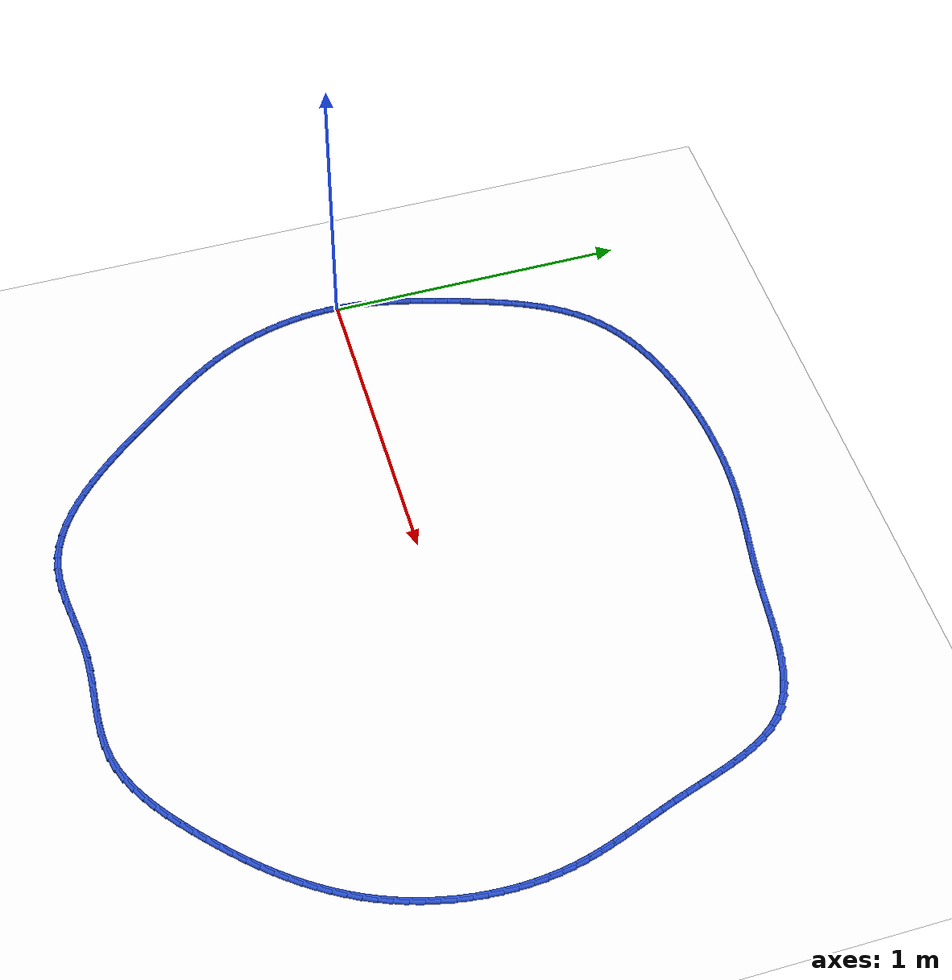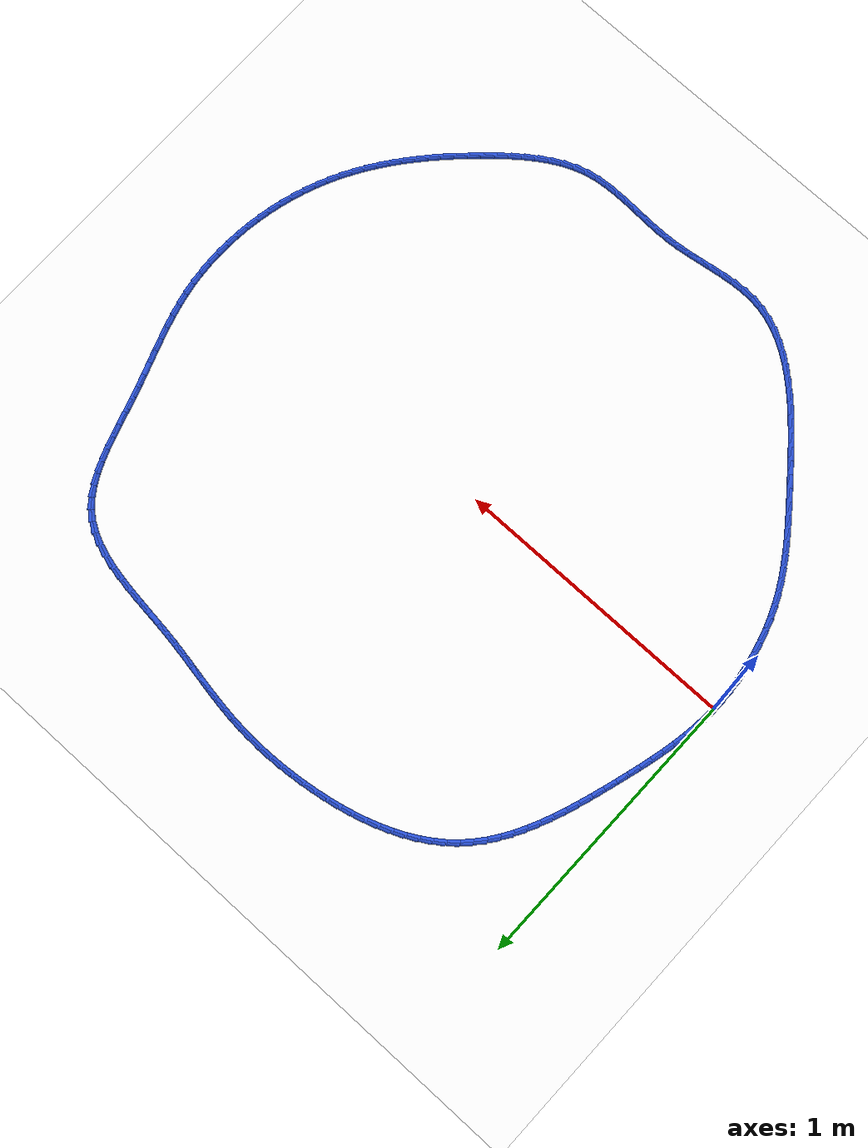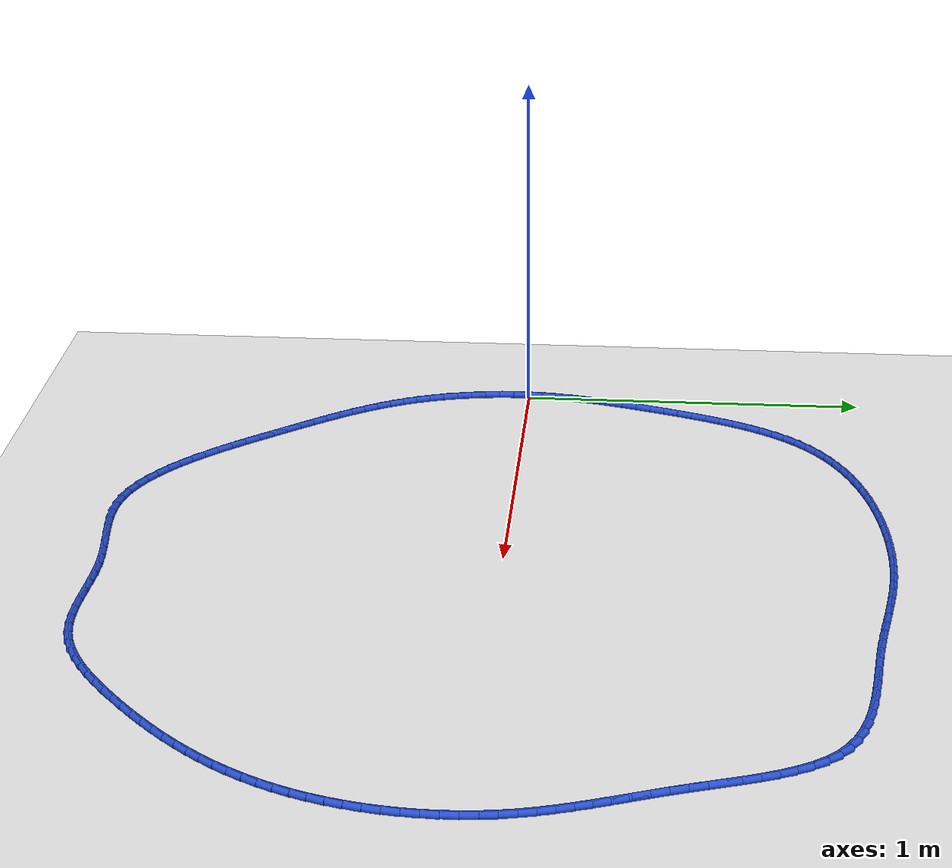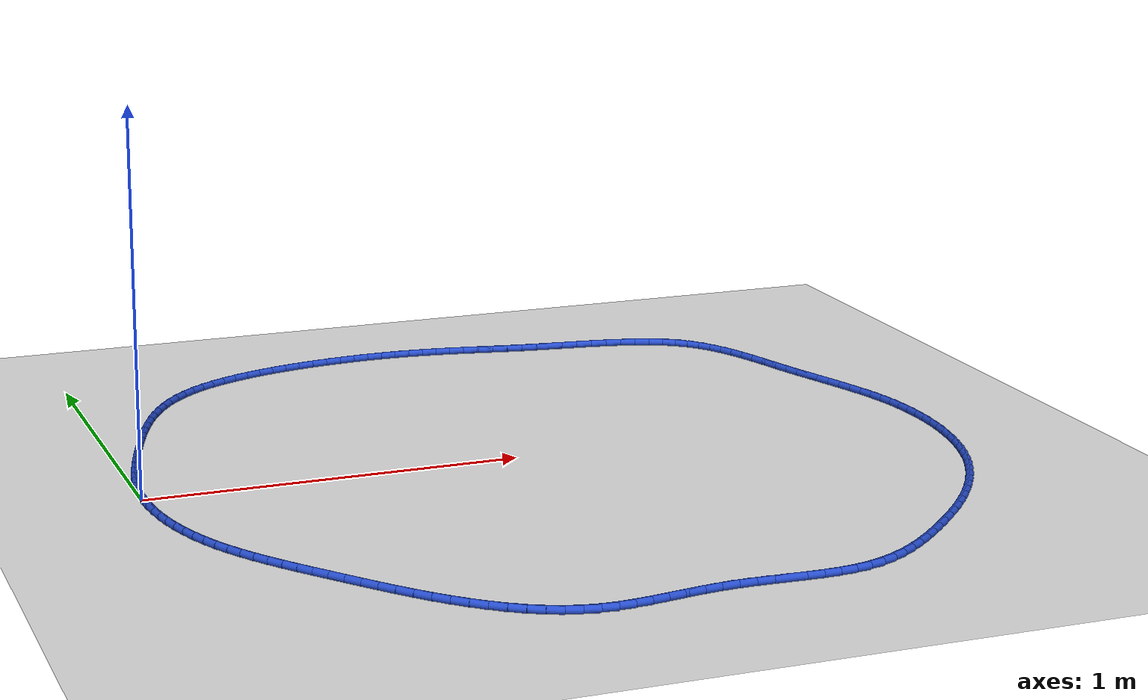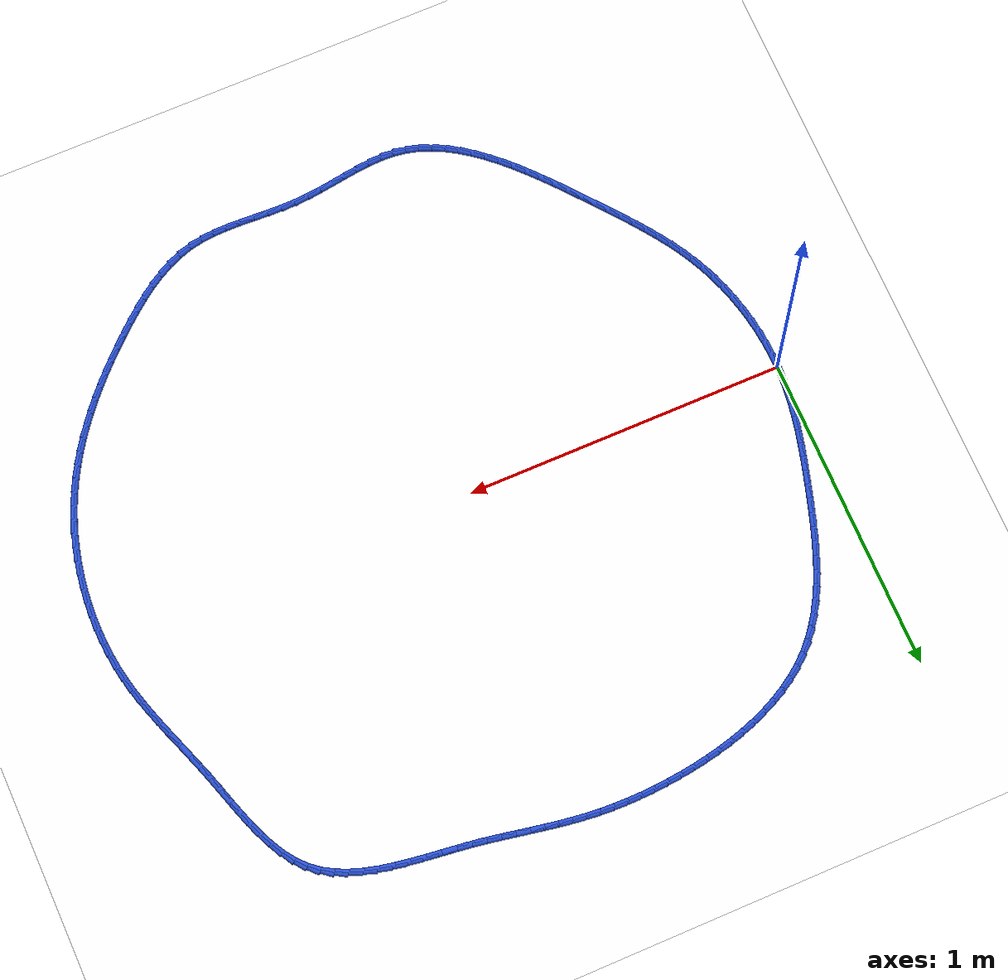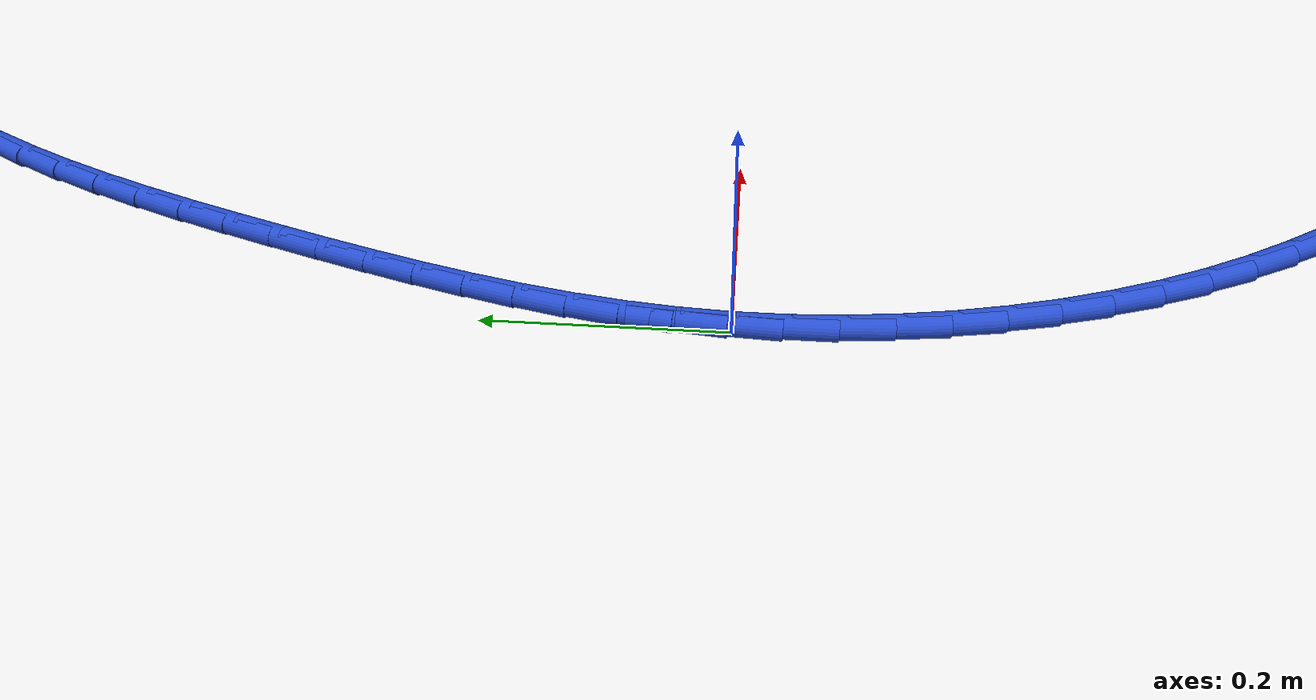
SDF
<sdf version="1.6">
 <world name="default">
  <light name="sun" type="directional">
   <pose>0 0 10 0 -0 0</pose>
   <diffuse>0.8 0.8 0.8 1</diffuse>
   <specular>0.2 0.2 0.2 1</specular>
   <attenuation>
    <range>1000</range>
    <constant>0.9</constant>
    <linear>0.01</linear>
    <quadratic>0.001</quadratic>
   </attenuation>
   <direction>-0.5 0.1 -0.9</direction>
  </light>
  <model name="ground_plane">
   <static>1</static>
   <link name="link">
    <collision name="collision">
     <geometry><plane><normal>0 0 1</normal><size>100 100</size></plane></geometry>
     <surface><friction><ode><mu>100</mu><mu2>50</mu2></ode></friction></surface>
    </collision>
    <visual name="visual">
     <cast_shadows>0</cast_shadows>
     <geometry><plane><normal>0 0 1</normal><size>100 100</size></plane></geometry>
     <material>
      <script><uri>file://media/materials/scripts/gazebo.material</uri><name>Gazebo/WhiteGlow</name></script>
     </material>
    </visual>
   </link>
  </model>
  <gravity>0 0 -9.8</gravity>
  <magnetic_field>6e-06 2.3e-05 -4.2e-05</magnetic_field>
  <atmosphere type="adiabatic"/>
  <physics name="default_physics" default="0" type="ode">
   <max_step_size>0.001</max_step_size>
   <real_time_factor>1</real_time_factor>
   <real_time_update_rate>1000</real_time_update_rate>
  </physics>
  <scene><ambient>0.4 0.4 0.4 1</ambient><background>0.7 0.7 0.7 1</background><shadows>1</shadows></scene>
  <spherical_coordinates>
   <surface_model>EARTH_WGS84</surface_model>
   <latitude_deg>0</latitude_deg>
   <longitude_deg>0</longitude_deg>
   <elevation>0</elevation>
   <heading_deg>0</heading_deg>
  </spherical_coordinates>
  <model name="line">
   <link name="link_0">
    <pose>1.734723475976807e-18 -6.938893903907228e-17 0.01 0 1.57 1.5186807041762862</pose>
    <collision name="collision">
     <geometry><cylinder><radius>0.01</radius><length>0.08</length></cylinder></geometry>
    </collision>
    <visual name="visual">
     <material>
      <script><name>Gazebo/Blue</name><uri>file://media/materials/scripts/gazebo.material</uri></script>
     </material>
     <geometry><cylinder><radius>0.01</radius><length>0.08</length></cylinder></geometry>
    </visual>
   </link>
   <link name="link_1">
    <pose>0.0022255702728750694 0.042665805088439646 0.01 0 1.57 1.4713120042472065</pose>
    <collision name="collision">
     <geometry><cylinder><radius>0.01</radius><length>0.08</length></cylinder></geometry>
    </collision>
    <visual name="visual">
     <material>
      <script><name>Gazebo/Blue</name><uri>file://media/materials/scripts/gazebo.material</uri></script>
     </material>
     <geometry><cylinder><radius>0.01</radius><length>0.08</length></cylinder></geometry>
    </visual>
   </link>
   <link name="link_2">
    <pose>0.0064519726637163625 0.08500865860821659 0.01 0 1.57 1.428681906047522</pose>
    <collision name="collision">
     <geometry><cylinder><radius>0.01</radius><length>0.08</length></cylinder></geometry>
    </collision>
    <visual name="visual">
     <material>
      <script><name>Gazebo/Blue</name><uri>file://media/materials/scripts/gazebo.material</uri></script>
     </material>
     <geometry><cylinder><radius>0.01</radius><length>0.08</length></cylinder></geometry>
    </visual>
   </link>
   <link name="link_3">
    <pose>0.012474710428388141 0.12710246544149936 0.01 0 1.57 1.3911044565387365</pose>
    <collision name="collision">
     <geometry><cylinder><radius>0.01</radius><length>0.08</length></cylinder></geometry>
    </collision>
    <visual name="visual">
     <material>
      <script><name>Gazebo/Blue</name><uri>file://media/materials/scripts/gazebo.material</uri></script>
     </material>
     <geometry><cylinder><radius>0.01</radius><length>0.08</length></cylinder></geometry>
    </visual>
   </link>
   <link name="link_4">
    <pose>0.02008928682275461 0.16902113047045642 0.01 0 1.57 1.3587648407987145</pose>
    <collision name="collision">
     <geometry><cylinder><radius>0.01</radius><length>0.08</length></cylinder></geometry>
    </collision>
    <visual name="visual">
     <material>
      <script><name>Gazebo/Blue</name><uri>file://media/materials/scripts/gazebo.material</uri></script>
     </material>
     <geometry><cylinder><radius>0.01</radius><length>0.08</length></cylinder></geometry>
    </visual>
   </link>
   <link name="link_5">
    <pose>0.029091205102680016 0.2108385585772562 0.01 0 1.57 1.3317441301647523</pose>
    <collision name="collision">
     <geometry><cylinder><radius>0.01</radius><length>0.08</length></cylinder></geometry>
    </collision>
    <visual name="visual">
     <material>
      <script><name>Gazebo/Blue</name><uri>file://media/materials/scripts/gazebo.material</uri></script>
     </material>
     <geometry><cylinder><radius>0.01</radius><length>0.08</length></cylinder></geometry>
    </visual>
   </link>
   <link name="link_6">
    <pose>0.03927596852402861 0.2526286546440673 0.01 0 1.57 1.3100451679042042</pose>
    <collision name="collision">
     <geometry><cylinder><radius>0.01</radius><length>0.08</length></cylinder></geometry>
    </collision>
    <visual name="visual">
     <material>
      <script><name>Gazebo/Blue</name><uri>file://media/materials/scripts/gazebo.material</uri></script>
     </material>
     <geometry><cylinder><radius>0.01</radius><length>0.08</length></cylinder></geometry>
    </visual>
   </link>
   <link name="link_7">
    <pose>0.05043908034266459 0.29446532355305816 0.01 0 1.57 1.2936162458024942</pose>
    <collision name="collision">
     <geometry><cylinder><radius>0.01</radius><length>0.08</length></cylinder></geometry>
    </collision>
    <visual name="visual">
     <material>
      <script><name>Gazebo/Blue</name><uri>file://media/materials/scripts/gazebo.material</uri></script>
     </material>
     <geometry><cylinder><radius>0.01</radius><length>0.08</length></cylinder></geometry>
    </visual>
   </link>
   <link name="link_8">
    <pose>0.06237604381445222 0.33642247018639726 0.01 0 1.57 1.2823706779399318</pose>
    <collision name="collision">
     <geometry><cylinder><radius>0.01</radius><length>0.08</length></cylinder></geometry>
    </collision>
    <visual name="visual">
     <material>
      <script><name>Gazebo/Blue</name><uri>file://media/materials/scripts/gazebo.material</uri></script>
     </material>
     <geometry><cylinder><radius>0.01</radius><length>0.08</length></cylinder></geometry>
    </visual>
   </link>
   <link name="link_9">
    <pose>0.0748823621952557 0.378573999426253 0.01 0 1.57 1.274912087369015</pose>
    <collision name="collision">
     <geometry><cylinder><radius>0.01</radius><length>0.08</length></cylinder></geometry>
    </collision>
    <visual name="visual">
     <material>
      <script><name>Gazebo/Blue</name><uri>file://media/materials/scripts/gazebo.material</uri></script>
     </material>
     <geometry><cylinder><radius>0.01</radius><length>0.08</length></cylinder></geometry>
    </visual>
   </link>
   <link name="link_10">
    <pose>0.08780163753450884 0.42095557310188564 0.01 0 1.57 1.264254248498636</pose>
    <collision name="collision">
     <geometry><cylinder><radius>0.01</radius><length>0.08</length></cylinder></geometry>
    </collision>
    <visual name="visual">
     <material>
      <script><name>Gazebo/Blue</name><uri>file://media/materials/scripts/gazebo.material</uri></script>
     </material>
     <geometry><cylinder><radius>0.01</radius><length>0.08</length></cylinder></geometry>
    </visual>
   </link>
   <link name="link_11">
    <pose>0.10123539991750542 0.4633977760585001 0.01 0 1.57 1.2480336119488133</pose>
    <collision name="collision">
     <geometry><cylinder><radius>0.01</radius><length>0.08</length></cylinder></geometry>
    </collision>
    <visual name="visual">
     <material>
      <script><name>Gazebo/Blue</name><uri>file://media/materials/scripts/gazebo.material</uri></script>
     </material>
     <geometry><cylinder><radius>0.01</radius><length>0.08</length></cylinder></geometry>
    </visual>
   </link>
   <link name="link_12">
    <pose>0.11537127035748558 0.505662742777621 0.01 0 1.57 1.226092957649024</pose>
    <collision name="collision">
     <geometry><cylinder><radius>0.01</radius><length>0.08</length></cylinder></geometry>
    </collision>
    <visual name="visual">
     <material>
      <script><name>Gazebo/Blue</name><uri>file://media/materials/scripts/gazebo.material</uri></script>
     </material>
     <geometry><cylinder><radius>0.01</radius><length>0.08</length></cylinder></geometry>
    </visual>
   </link>
   <link name="link_13">
    <pose>0.13039692985673074 0.5475125600438586 0.01 0 1.57 1.1981736653455037</pose>
    <collision name="collision">
     <geometry><cylinder><radius>0.01</radius><length>0.08</length></cylinder></geometry>
    </collision>
    <visual name="visual">
     <material>
      <script><name>Gazebo/Blue</name><uri>file://media/materials/scripts/gazebo.material</uri></script>
     </material>
     <geometry><cylinder><radius>0.01</radius><length>0.08</length></cylinder></geometry>
    </visual>
   </link>
   <link name="link_14">
    <pose>0.14650005941752228 0.588709314641823 0.01 0 1.57 1.1639280657971418</pose>
    <collision name="collision">
     <geometry><cylinder><radius>0.01</radius><length>0.08</length></cylinder></geometry>
    </collision>
    <visual name="visual">
     <material>
      <script><name>Gazebo/Blue</name><uri>file://media/materials/scripts/gazebo.material</uri></script>
     </material>
     <geometry><cylinder><radius>0.01</radius><length>0.08</length></cylinder></geometry>
    </visual>
   </link>
   <link name="link_15">
    <pose>0.16386834004214154 0.6290150933561237 0.01 0 1.57 1.1229402111961178</pose>
    <collision name="collision">
     <geometry><cylinder><radius>0.01</radius><length>0.08</length></cylinder></geometry>
    </collision>
    <visual name="visual">
     <material>
      <script><name>Gazebo/Blue</name><uri>file://media/materials/scripts/gazebo.material</uri></script>
     </material>
     <geometry><cylinder><radius>0.01</radius><length>0.08</length></cylinder></geometry>
    </visual>
   </link>
   <link name="link_16">
    <pose>0.18268945273286996 0.6681919829713713 0.01 0 1.57 1.074758864009648</pose>
    <collision name="collision">
     <geometry><cylinder><radius>0.01</radius><length>0.08</length></cylinder></geometry>
    </collision>
    <visual name="visual">
     <material>
      <script><name>Gazebo/Blue</name><uri>file://media/materials/scripts/gazebo.material</uri></script>
     </material>
     <geometry><cylinder><radius>0.01</radius><length>0.08</length></cylinder></geometry>
    </visual>
   </link>
   <link name="link_17">
    <pose>0.20315107849198888 0.7060020702721752 0.01 0 1.57 1.0189492243153868</pose>
    <collision name="collision">
     <geometry><cylinder><radius>0.01</radius><length>0.08</length></cylinder></geometry>
    </collision>
    <visual name="visual">
     <material>
      <script><name>Gazebo/Blue</name><uri>file://media/materials/scripts/gazebo.material</uri></script>
     </material>
     <geometry><cylinder><radius>0.01</radius><length>0.08</length></cylinder></geometry>
    </visual>
   </link>
   <link name="link_18">
    <pose>0.2254408983217796 0.7422074420431457 0.01 0 1.57 0.9551698408678385</pose>
    <collision name="collision">
     <geometry><cylinder><radius>0.01</radius><length>0.08</length></cylinder></geometry>
    </collision>
    <visual name="visual">
     <material>
      <script><name>Gazebo/Blue</name><uri>file://media/materials/scripts/gazebo.material</uri></script>
     </material>
     <geometry><cylinder><radius>0.01</radius><length>0.08</length></cylinder></geometry>
    </visual>
   </link>
   <link name="link_19">
    <pose>0.24974659322452367 0.7765701850688925 0.01 0 1.57 0.8832780800777653</pose>
    <collision name="collision">
     <geometry><cylinder><radius>0.01</radius><length>0.08</length></cylinder></geometry>
    </collision>
    <visual name="visual">
     <material>
      <script><name>Gazebo/Blue</name><uri>file://media/materials/scripts/gazebo.material</uri></script>
     </material>
     <geometry><cylinder><radius>0.01</radius><length>0.08</length></cylinder></geometry>
    </visual>
   </link>
   <link name="link_20">
    <pose>0.2762558442025023 0.808852386134026 0.01 0 1.57 0.8034591398518491</pose>
    <collision name="collision">
     <geometry><cylinder><radius>0.01</radius><length>0.08</length></cylinder></geometry>
    </collision>
    <visual name="visual">
     <material>
      <script><name>Gazebo/Blue</name><uri>file://media/materials/scripts/gazebo.material</uri></script>
     </material>
     <geometry><cylinder><radius>0.01</radius><length>0.08</length></cylinder></geometry>
    </visual>
   </link>
   <link name="link_21">
    <pose>0.3051563304087328 0.8388161334906852 0.01 0 1.57 0.7186803359185121</pose>
    <collision name="collision">
     <geometry><cylinder><radius>0.01</radius><length>0.08</length></cylinder></geometry>
    </collision>
    <visual name="visual">
     <material>
      <script><name>Gazebo/Blue</name><uri>file://media/materials/scripts/gazebo.material</uri></script>
     </material>
     <geometry><cylinder><radius>0.01</radius><length>0.08</length></cylinder></geometry>
    </visual>
   </link>
   <link name="link_22">
    <pose>0.3365585413730784 0.8662847711374708 0.01 0 1.57 0.638207192442804</pose>
    <collision name="collision">
     <geometry><cylinder><radius>0.01</radius><length>0.08</length></cylinder></geometry>
    </collision>
    <visual name="visual">
     <material>
      <script><name>Gazebo/Blue</name><uri>file://media/materials/scripts/gazebo.material</uri></script>
     </material>
     <geometry><cylinder><radius>0.01</radius><length>0.08</length></cylinder></geometry>
    </visual>
   </link>
   <link name="link_23">
    <pose>0.3702904886991473 0.8913058104613497 0.01 0 1.57 0.5642304448531043</pose>
    <collision name="collision">
     <geometry><cylinder><radius>0.01</radius><length>0.08</length></cylinder></geometry>
    </collision>
    <visual name="visual">
     <material>
      <script><name>Gazebo/Blue</name><uri>file://media/materials/scripts/gazebo.material</uri></script>
     </material>
     <geometry><cylinder><radius>0.01</radius><length>0.08</length></cylinder></geometry>
    </visual>
   </link>
   <link name="link_24">
    <pose>0.4061155841111592 0.9139780276912653 0.01 0 1.57 0.4966540611262847</pose>
    <collision name="collision">
     <geometry><cylinder><radius>0.01</radius><length>0.08</length></cylinder></geometry>
    </collision>
    <visual name="visual">
     <material>
      <script><name>Gazebo/Blue</name><uri>file://media/materials/scripts/gazebo.material</uri></script>
     </material>
     <geometry><cylinder><radius>0.01</radius><length>0.08</length></cylinder></geometry>
    </visual>
   </link>
   <link name="link_25">
    <pose>0.4437972393333336 0.9344001990561615 0.01 0 1.57 0.435166565494479</pose>
    <collision name="collision">
     <geometry><cylinder><radius>0.01</radius><length>0.08</length></cylinder></geometry>
    </collision>
    <visual name="visual">
     <material>
      <script><name>Gazebo/Blue</name><uri>file://media/materials/scripts/gazebo.material</uri></script>
     </material>
     <geometry><cylinder><radius>0.01</radius><length>0.08</length></cylinder></geometry>
    </visual>
   </link>
   <link name="link_26">
    <pose>0.4830988660898901 0.9526711007849819 0.01 0 1.57 0.37932781316289005</pose>
    <collision name="collision">
     <geometry><cylinder><radius>0.01</radius><length>0.08</length></cylinder></geometry>
    </collision>
    <visual name="visual">
     <material>
      <script><name>Gazebo/Blue</name><uri>file://media/materials/scripts/gazebo.material</uri></script>
     </material>
     <geometry><cylinder><radius>0.01</radius><length>0.08</length></cylinder></geometry>
    </visual>
   </link>
   <link name="link_27">
    <pose>0.5237838761050482 0.9688895091066698 0.01 0 1.57 0.32863558943300447</pose>
    <collision name="collision">
     <geometry><cylinder><radius>0.01</radius><length>0.08</length></cylinder></geometry>
    </collision>
    <visual name="visual">
     <material>
      <script><name>Gazebo/Blue</name><uri>file://media/materials/scripts/gazebo.material</uri></script>
     </material>
     <geometry><cylinder><radius>0.01</radius><length>0.08</length></cylinder></geometry>
    </visual>
   </link>
   <link name="link_28">
    <pose>0.5656156811030278 0.9831542002501699 0.01 0 1.57 0.28257176241104004</pose>
    <collision name="collision">
     <geometry><cylinder><radius>0.01</radius><length>0.08</length></cylinder></geometry>
    </collision>
    <visual name="visual">
     <material>
      <script><name>Gazebo/Blue</name><uri>file://media/materials/scripts/gazebo.material</uri></script>
     </material>
     <geometry><cylinder><radius>0.01</radius><length>0.08</length></cylinder></geometry>
    </visual>
   </link>
   <link name="link_29">
    <pose>0.6083576928080481 0.9955639504444246 0.01 0 1.57 0.24063133174145582</pose>
    <collision name="collision">
     <geometry><cylinder><radius>0.01</radius><length>0.08</length></cylinder></geometry>
    </collision>
    <visual name="visual">
     <material>
      <script><name>Gazebo/Blue</name><uri>file://media/materials/scripts/gazebo.material</uri></script>
     </material>
     <geometry><cylinder><radius>0.01</radius><length>0.08</length></cylinder></geometry>
    </visual>
   </link>
   <link name="link_30">
    <pose>0.6517733229443284 1.0062175359183783 0.01 0 1.57 0.20233868571714028</pose>
    <collision name="collision">
     <geometry><cylinder><radius>0.01</radius><length>0.08</length></cylinder></geometry>
    </collision>
    <visual name="visual">
     <material>
      <script><name>Gazebo/Blue</name><uri>file://media/materials/scripts/gazebo.material</uri></script>
     </material>
     <geometry><cylinder><radius>0.01</radius><length>0.08</length></cylinder></geometry>
    </visual>
   </link>
   <link name="link_31">
    <pose>0.6956259832360889 1.0152137329009747 0.01 0 1.57 0.16725499663702917</pose>
    <collision name="collision">
     <geometry><cylinder><radius>0.01</radius><length>0.08</length></cylinder></geometry>
    </collision>
    <visual name="visual">
     <material>
      <script><name>Gazebo/Blue</name><uri>file://media/materials/scripts/gazebo.material</uri></script>
     </material>
     <geometry><cylinder><radius>0.01</radius><length>0.08</length></cylinder></geometry>
    </visual>
   </link>
   <link name="link_32">
    <pose>0.7396790854075489 1.0226513176211571 0.01 0 1.57 0.13497981500120357</pose>
    <collision name="collision">
     <geometry><cylinder><radius>0.01</radius><length>0.08</length></cylinder></geometry>
    </collision>
    <visual name="visual">
     <material>
      <script><name>Gazebo/Blue</name><uri>file://media/materials/scripts/gazebo.material</uri></script>
     </material>
     <geometry><cylinder><radius>0.01</radius><length>0.08</length></cylinder></geometry>
    </visual>
   </link>
   <link name="link_33">
    <pose>0.7836960411859901 1.0286290663064284 0.01 0 1.57 0.10464812955575604</pose>
    <collision name="collision">
     <geometry><cylinder><radius>0.01</radius><length>0.08</length></cylinder></geometry>
    </collision>
    <visual name="visual">
     <material>
      <script><name>Gazebo/Blue</name><uri>file://media/materials/scripts/gazebo.material</uri></script>
     </material>
     <geometry><cylinder><radius>0.01</radius><length>0.08</length></cylinder></geometry>
    </visual>
   </link>
   <link name="link_34">
    <pose>0.8274787454387937 1.0332276433751173 0.01 0 1.57 0.0740799324541237</pose>
    <collision name="collision">
     <geometry><cylinder><radius>0.01</radius><length>0.08</length></cylinder></geometry>
    </collision>
    <visual name="visual">
     <material>
      <script><name>Gazebo/Blue</name><uri>file://media/materials/scripts/gazebo.material</uri></script>
     </material>
     <geometry><cylinder><radius>0.01</radius><length>0.08</length></cylinder></geometry>
    </visual>
   </link>
   <link name="link_35">
    <pose>0.8709810436834522 1.036456198780478 0.01 0 1.57 0.04278564622942004</pose>
    <collision name="collision">
     <geometry><cylinder><radius>0.01</radius><length>0.08</length></cylinder></geometry>
    </collision>
    <visual name="visual">
     <material>
      <script><name>Gazebo/Blue</name><uri>file://media/materials/scripts/gazebo.material</uri></script>
     </material>
     <geometry><cylinder><radius>0.01</radius><length>0.08</length></cylinder></geometry>
    </visual>
   </link>
   <link name="link_36">
    <pose>0.9141942799853213 1.038306234057746 0.01 0 1.57 0.010788608343496257</pose>
    <collision name="collision">
     <geometry><cylinder><radius>0.01</radius><length>0.08</length></cylinder></geometry>
    </collision>
    <visual name="visual">
     <material>
      <script><name>Gazebo/Blue</name><uri>file://media/materials/scripts/gazebo.material</uri></script>
     </material>
     <geometry><cylinder><radius>0.01</radius><length>0.08</length></cylinder></geometry>
    </visual>
   </link>
   <link name="link_37">
    <pose>0.9571097984097561 1.0387692507421569 0.01 0 1.57 -0.021881489290993806</pose>
    <collision name="collision">
     <geometry><cylinder><radius>0.01</radius><length>0.08</length></cylinder></geometry>
    </collision>
    <visual name="visual">
     <material>
      <script><name>Gazebo/Blue</name><uri>file://media/materials/scripts/gazebo.material</uri></script>
     </material>
     <geometry><cylinder><radius>0.01</radius><length>0.08</length></cylinder></geometry>
    </visual>
   </link>
   <link name="link_38">
    <pose>0.9997189430221121 1.0378367503689454 0.01 0 1.57 -0.05518837002799684</pose>
    <collision name="collision">
     <geometry><cylinder><radius>0.01</radius><length>0.08</length></cylinder></geometry>
    </collision>
    <visual name="visual">
     <material>
      <script><name>Gazebo/Blue</name><uri>file://media/materials/scripts/gazebo.material</uri></script>
     </material>
     <geometry><cylinder><radius>0.01</radius><length>0.08</length></cylinder></geometry>
    </visual>
   </link>
   <link name="link_39">
    <pose>1.0420130578877438 1.0355002344733468 0.01 0 1.57 -0.08908906089191951</pose>
    <collision name="collision">
     <geometry><cylinder><radius>0.01</radius><length>0.08</length></cylinder></geometry>
    </collision>
    <visual name="visual">
     <material>
      <script><name>Gazebo/Blue</name><uri>file://media/materials/scripts/gazebo.material</uri></script>
     </material>
     <geometry><cylinder><radius>0.01</radius><length>0.08</length></cylinder></geometry>
    </visual>
   </link>
   <link name="link_40">
    <pose>1.083983487072007 1.0317512045905965 0.01 0 1.57 -0.12247822357086942</pose>
    <collision name="collision">
     <geometry><cylinder><radius>0.01</radius><length>0.08</length></cylinder></geometry>
    </collision>
    <visual name="visual">
     <material>
      <script><name>Gazebo/Blue</name><uri>file://media/materials/scripts/gazebo.material</uri></script>
     </material>
     <geometry><cylinder><radius>0.01</radius><length>0.08</length></cylinder></geometry>
    </visual>
   </link>
   <link name="link_41">
    <pose>1.125646442639785 1.02662273018511 0.01 0 1.57 -0.1500103768400907</pose>
    <collision name="collision">
     <geometry><cylinder><radius>0.01</radius><length>0.08</length></cylinder></geometry>
    </collision>
    <visual name="visual">
     <material>
      <script><name>Gazebo/Blue</name><uri>file://media/materials/scripts/gazebo.material</uri></script>
     </material>
     <geometry><cylinder><radius>0.01</radius><length>0.08</length></cylinder></geometry>
    </visual>
   </link>
   <link name="link_42">
    <pose>1.1671397648547246 1.0203511874789246 0.01 0 1.57 -0.16982790035343945</pose>
    <collision name="collision">
     <geometry><cylinder><radius>0.01</radius><length>0.08</length></cylinder></geometry>
    </collision>
    <visual name="visual">
     <material>
      <script><name>Gazebo/Blue</name><uri>file://media/materials/scripts/gazebo.material</uri></script>
     </material>
     <geometry><cylinder><radius>0.01</radius><length>0.08</length></cylinder></geometry>
    </visual>
   </link>
   <link name="link_43">
    <pose>1.2086384210378591 1.01323501216494 0.01 0 1.57 -0.18181214256237524</pose>
    <collision name="collision">
     <geometry><cylinder><radius>0.01</radius><length>0.08</length></cylinder></geometry>
    </collision>
    <visual name="visual">
     <material>
      <script><name>Gazebo/Blue</name><uri>file://media/materials/scripts/gazebo.material</uri></script>
     </material>
     <geometry><cylinder><radius>0.01</radius><length>0.08</length></cylinder></geometry>
    </visual>
   </link>
   <link name="link_44">
    <pose>1.2503173876569167 1.0055726552251478 0.01 0 1.57 -0.18600665311869785</pose>
    <collision name="collision">
     <geometry><cylinder><radius>0.01</radius><length>0.08</length></cylinder></geometry>
    </collision>
    <visual name="visual">
     <material>
      <script><name>Gazebo/Blue</name><uri>file://media/materials/scripts/gazebo.material</uri></script>
     </material>
     <geometry><cylinder><radius>0.01</radius><length>0.08</length></cylinder></geometry>
    </visual>
   </link>
   <link name="link_45">
    <pose>1.292351641179624 0.9976625676415394 0.01 0 1.57 -0.18258944699541996</pose>
    <collision name="collision">
     <geometry><cylinder><radius>0.01</radius><length>0.08</length></cylinder></geometry>
    </collision>
    <visual name="visual">
     <material>
      <script><name>Gazebo/Blue</name><uri>file://media/materials/scripts/gazebo.material</uri></script>
     </material>
     <geometry><cylinder><radius>0.01</radius><length>0.08</length></cylinder></geometry>
    </visual>
   </link>
   <link name="link_46">
    <pose>1.3349161580737092 0.9898032003961066 0.01 0 1.57 -0.17185477720959072</pose>
    <collision name="collision">
     <geometry><cylinder><radius>0.01</radius><length>0.08</length></cylinder></geometry>
    </collision>
    <visual name="visual">
     <material>
      <script><name>Gazebo/Blue</name><uri>file://media/materials/scripts/gazebo.material</uri></script>
     </material>
     <geometry><cylinder><radius>0.01</radius><length>0.08</length></cylinder></geometry>
    </visual>
   </link>
   <link name="link_47">
    <pose>1.3781859148068998 0.9822930044708411 0.01 0 1.57 -0.15420377702841706</pose>
    <collision name="collision">
     <geometry><cylinder><radius>0.01</radius><length>0.08</length></cylinder></geometry>
    </collision>
    <visual name="visual">
     <material>
      <script><name>Gazebo/Blue</name><uri>file://media/materials/scripts/gazebo.material</uri></script>
     </material>
     <geometry><cylinder><radius>0.01</radius><length>0.08</length></cylinder></geometry>
    </visual>
   </link>
   <link name="link_48">
    <pose>1.4223358878469228 0.975430430847734 0.01 0 1.57 -0.13317774749445782</pose>
    <collision name="collision">
     <geometry><cylinder><radius>0.01</radius><length>0.08</length></cylinder></geometry>
    </collision>
    <visual name="visual">
     <material>
      <script><name>Gazebo/Blue</name><uri>file://media/materials/scripts/gazebo.material</uri></script>
     </material>
     <geometry><cylinder><radius>0.01</radius><length>0.08</length></cylinder></geometry>
    </visual>
   </link>
   <link name="link_49">
    <pose>1.4674420356015716 0.9693875271003631 0.01 0 1.57 -0.12176923726375755</pose>
    <collision name="collision">
     <geometry><cylinder><radius>0.01</radius><length>0.08</length></cylinder></geometry>
    </collision>
    <visual name="visual">
     <material>
      <script><name>Gazebo/Blue</name><uri>file://media/materials/scripts/gazebo.material</uri></script>
     </material>
     <geometry><cylinder><radius>0.01</radius><length>0.08</length></cylinder></geometry>
    </visual>
   </link>
   <link name="link_50">
    <pose>1.5131550162277354 0.9637934155889678 0.01 0 1.57 -0.12284945178763806</pose>
    <collision name="collision">
     <geometry><cylinder><radius>0.01</radius><length>0.08</length></cylinder></geometry>
    </collision>
    <visual name="visual">
     <material>
      <script><name>Gazebo/Blue</name><uri>file://media/materials/scripts/gazebo.material</uri></script>
     </material>
     <geometry><cylinder><radius>0.01</radius><length>0.08</length></cylinder></geometry>
    </visual>
   </link>
   <link name="link_51">
    <pose>1.5590113245453074 0.9581314812707133 0.01 0 1.57 -0.13632321833527564</pose>
    <collision name="collision">
     <geometry><cylinder><radius>0.01</radius><length>0.08</length></cylinder></geometry>
    </collision>
    <visual name="visual">
     <material>
      <script><name>Gazebo/Blue</name><uri>file://media/materials/scripts/gazebo.material</uri></script>
     </material>
     <geometry><cylinder><radius>0.01</radius><length>0.08</length></cylinder></geometry>
    </visual>
   </link>
   <link name="link_52">
    <pose>1.604547453953074 0.9518851072886262 0.01 0 1.57 -0.16272768667551943</pose>
    <collision name="collision">
     <geometry><cylinder><radius>0.01</radius><length>0.08</length></cylinder></geometry>
    </collision>
    <visual name="visual">
     <material>
      <script><name>Gazebo/Blue</name><uri>file://media/materials/scripts/gazebo.material</uri></script>
     </material>
     <geometry><cylinder><radius>0.01</radius><length>0.08</length></cylinder></geometry>
    </visual>
   </link>
   <link name="link_53">
    <pose>1.6492998978498241 0.9445376767857319 0.01 0 1.57 -0.20322471222318544</pose>
    <collision name="collision">
     <geometry><cylinder><radius>0.01</radius><length>0.08</length></cylinder></geometry>
    </collision>
    <visual name="visual">
     <material>
      <script><name>Gazebo/Blue</name><uri>file://media/materials/scripts/gazebo.material</uri></script>
     </material>
     <geometry><cylinder><radius>0.01</radius><length>0.08</length></cylinder></geometry>
    </visual>
   </link>
   <link name="link_54">
    <pose>1.6928051496343446 0.9355725729050577 0.01 0 1.57 -0.2595785811376601</pose>
    <collision name="collision">
     <geometry><cylinder><radius>0.01</radius><length>0.08</length></cylinder></geometry>
    </collision>
    <visual name="visual">
     <material>
      <script><name>Gazebo/Blue</name><uri>file://media/materials/scripts/gazebo.material</uri></script>
     </material>
     <geometry><cylinder><radius>0.01</radius><length>0.08</length></cylinder></geometry>
    </visual>
   </link>
   <link name="link_55">
    <pose>1.7345997027054234 0.9244731787896288 0.01 0 1.57 -0.3340456842501688</pose>
    <collision name="collision">
     <geometry><cylinder><radius>0.01</radius><length>0.08</length></cylinder></geometry>
    </collision>
    <visual name="visual">
     <material>
      <script><name>Gazebo/Blue</name><uri>file://media/materials/scripts/gazebo.material</uri></script>
     </material>
     <geometry><cylinder><radius>0.01</radius><length>0.08</length></cylinder></geometry>
    </visual>
   </link>
   <link name="link_56">
    <pose>1.7742200504618484 0.9107228775824721 0.01 0 1.57 -0.4290346965300316</pose>
    <collision name="collision">
     <geometry><cylinder><radius>0.01</radius><length>0.08</length></cylinder></geometry>
    </collision>
    <visual name="visual">
     <material>
      <script><name>Gazebo/Blue</name><uri>file://media/materials/scripts/gazebo.material</uri></script>
     </material>
     <geometry><cylinder><radius>0.01</radius><length>0.08</length></cylinder></geometry>
    </visual>
   </link>
   <link name="link_57">
    <pose>1.8112026863024073 0.8938050524266137 0.01 0 1.57 -0.5463255784357631</pose>
    <collision name="collision">
     <geometry><cylinder><radius>0.01</radius><length>0.08</length></cylinder></geometry>
    </collision>
    <visual name="visual">
     <material>
      <script><name>Gazebo/Blue</name><uri>file://media/materials/scripts/gazebo.material</uri></script>
     </material>
     <geometry><cylinder><radius>0.01</radius><length>0.08</length></cylinder></geometry>
    </visual>
   </link>
   <link name="link_58">
    <pose>1.8450841036258883 0.8732030864650793 0.01 0 1.57 -0.6856668858034809</pose>
    <collision name="collision">
     <geometry><cylinder><radius>0.01</radius><length>0.08</length></cylinder></geometry>
    </collision>
    <visual name="visual">
     <material>
      <script><name>Gazebo/Blue</name><uri>file://media/materials/scripts/gazebo.material</uri></script>
     </material>
     <geometry><cylinder><radius>0.01</radius><length>0.08</length></cylinder></geometry>
    </visual>
   </link>
   <link name="link_59">
    <pose>1.8754014627115032 0.8484011439334741 0.01 0 1.57 -0.8335406833218331</pose>
    <collision name="collision">
     <geometry><cylinder><radius>0.01</radius><length>0.08</length></cylinder></geometry>
    </collision>
    <visual name="visual">
     <material>
      <script><name>Gazebo/Blue</name><uri>file://media/materials/scripts/gazebo.material</uri></script>
     </material>
     <geometry><cylinder><radius>0.01</radius><length>0.08</length></cylinder></geometry>
    </visual>
   </link>
   <link name="link_60">
    <pose>1.9019408674390639 0.8191749675743611 0.01 0 1.57 -0.9607762577123368</pose>
    <collision name="collision">
     <geometry><cylinder><radius>0.01</radius><length>0.08</length></cylinder></geometry>
    </collision>
    <visual name="visual">
     <material>
      <script><name>Gazebo/Blue</name><uri>file://media/materials/scripts/gazebo.material</uri></script>
     </material>
     <geometry><cylinder><radius>0.01</radius><length>0.08</length></cylinder></geometry>
    </visual>
   </link>
   <link name="link_61">
    <pose>1.9251092667372205 0.7860274731604934 0.01 0 1.57 -1.06271174624357</pose>
    <collision name="collision">
     <geometry><cylinder><radius>0.01</radius><length>0.08</length></cylinder></geometry>
    </collision>
    <visual name="visual">
     <material>
      <script><name>Gazebo/Blue</name><uri>file://media/materials/scripts/gazebo.material</uri></script>
     </material>
     <geometry><cylinder><radius>0.01</radius><length>0.08</length></cylinder></geometry>
    </visual>
   </link>
   <link name="link_62">
    <pose>1.9454087881941964 0.749573055736984 0.01 0 1.57 -1.14123627584994</pose>
    <collision name="collision">
     <geometry><cylinder><radius>0.01</radius><length>0.08</length></cylinder></geometry>
    </collision>
    <visual name="visual">
     <material>
      <script><name>Gazebo/Blue</name><uri>file://media/materials/scripts/gazebo.material</uri></script>
     </material>
     <geometry><cylinder><radius>0.01</radius><length>0.08</length></cylinder></geometry>
    </visual>
   </link>
   <link name="link_63">
    <pose>1.963341559398216 0.7104261103489455 0.01 0 1.57 -1.1991430675300023</pose>
    <collision name="collision">
     <geometry><cylinder><radius>0.01</radius><length>0.08</length></cylinder></geometry>
    </collision>
    <visual name="visual">
     <material>
      <script><name>Gazebo/Blue</name><uri>file://media/materials/scripts/gazebo.material</uri></script>
     </material>
     <geometry><cylinder><radius>0.01</radius><length>0.08</length></cylinder></geometry>
    </visual>
   </link>
   <link name="link_64">
    <pose>1.9794097079375028 0.6692010320414907 0.01 0 1.57 -1.23904314193811</pose>
    <collision name="collision">
     <geometry><cylinder><radius>0.01</radius><length>0.08</length></cylinder></geometry>
    </collision>
    <visual name="visual">
     <material>
      <script><name>Gazebo/Blue</name><uri>file://media/materials/scripts/gazebo.material</uri></script>
     </material>
     <geometry><cylinder><radius>0.01</radius><length>0.08</length></cylinder></geometry>
    </visual>
   </link>
   <link name="link_65">
    <pose>1.9941153614002813 0.6265122158597322 0.01 0 1.57 -1.2629054993938276</pose>
    <collision name="collision">
     <geometry><cylinder><radius>0.01</radius><length>0.08</length></cylinder></geometry>
    </collision>
    <visual name="visual">
     <material>
      <script><name>Gazebo/Blue</name><uri>file://media/materials/scripts/gazebo.material</uri></script>
     </material>
     <geometry><cylinder><radius>0.01</radius><length>0.08</length></cylinder></geometry>
    </visual>
   </link>
   <link name="link_66">
    <pose>2.0079606473747766 0.5829740568487822 0.01 0 1.57 -1.271913490997217</pose>
    <collision name="collision">
     <geometry><cylinder><radius>0.01</radius><length>0.08</length></cylinder></geometry>
    </collision>
    <visual name="visual">
     <material>
      <script><name>Gazebo/Blue</name><uri>file://media/materials/scripts/gazebo.material</uri></script>
     </material>
     <geometry><cylinder><radius>0.01</radius><length>0.08</length></cylinder></geometry>
    </visual>
   </link>
   <link name="link_67">
    <pose>2.0214476934492116 0.5392009500537542 0.01 0 1.57 -1.2664338048668256</pose>
    <collision name="collision">
     <geometry><cylinder><radius>0.01</radius><length>0.08</length></cylinder></geometry>
    </collision>
    <visual name="visual">
     <material>
      <script><name>Gazebo/Blue</name><uri>file://media/materials/scripts/gazebo.material</uri></script>
     </material>
     <geometry><cylinder><radius>0.01</radius><length>0.08</length></cylinder></geometry>
    </visual>
   </link>
   <link name="link_68">
    <pose>2.03507862721181 0.4958072905197601 0.01 0 1.57 -1.2495818379929884</pose>
    <collision name="collision">
     <geometry><cylinder><radius>0.01</radius><length>0.08</length></cylinder></geometry>
    </collision>
    <visual name="visual">
     <material>
      <script><name>Gazebo/Blue</name><uri>file://media/materials/scripts/gazebo.material</uri></script>
     </material>
     <geometry><cylinder><radius>0.01</radius><length>0.08</length></cylinder></geometry>
    </visual>
   </link>
   <link name="link_69">
    <pose>2.049229341183821 0.4532791692977599 0.01 0 1.57 -1.2356742938745477</pose>
    <collision name="collision">
     <geometry><cylinder><radius>0.01</radius><length>0.08</length></cylinder></geometry>
    </collision>
    <visual name="visual">
     <material>
      <script><name>Gazebo/Blue</name><uri>file://media/materials/scripts/gazebo.material</uri></script>
     </material>
     <geometry><cylinder><radius>0.01</radius><length>0.08</length></cylinder></geometry>
    </visual>
   </link>
   <link name="link_70">
    <pose>2.0637540408442923 0.4115724402168727 0.01 0 1.57 -1.2288189067762425</pose>
    <collision name="collision">
     <geometry><cylinder><radius>0.01</radius><length>0.08</length></cylinder></geometry>
    </collision>
    <visual name="visual">
     <material>
      <script><name>Gazebo/Blue</name><uri>file://media/materials/scripts/gazebo.material</uri></script>
     </material>
     <geometry><cylinder><radius>0.01</radius><length>0.08</length></cylinder></geometry>
    </visual>
   </link>
   <link name="link_71">
    <pose>2.0783721852925976 0.37050600230337233 0.01 0 1.57 -1.2293357264124927</pose>
    <collision name="collision">
     <geometry><cylinder><radius>0.01</radius><length>0.08</length></cylinder></geometry>
    </collision>
    <visual name="visual">
     <material>
      <script><name>Gazebo/Blue</name><uri>file://media/materials/scripts/gazebo.material</uri></script>
     </material>
     <geometry><cylinder><radius>0.01</radius><length>0.08</length></cylinder></geometry>
    </visual>
   </link>
   <link name="link_72">
    <pose>2.092803233460333 0.3298987544130059 0.01 0 1.57 -1.2374785730630937</pose>
    <collision name="collision">
     <geometry><cylinder><radius>0.01</radius><length>0.08</length></cylinder></geometry>
    </collision>
    <visual name="visual">
     <material>
      <script><name>Gazebo/Blue</name><uri>file://media/materials/scripts/gazebo.material</uri></script>
     </material>
     <geometry><cylinder><radius>0.01</radius><length>0.08</length></cylinder></geometry>
    </visual>
   </link>
   <link name="link_73">
    <pose>2.106766644279096 0.28956959540151983 0.01 0 1.57 -1.2534253010028966</pose>
    <collision name="collision">
     <geometry><cylinder><radius>0.01</radius><length>0.08</length></cylinder></geometry>
    </collision>
    <visual name="visual">
     <material>
      <script><name>Gazebo/Blue</name><uri>file://media/materials/scripts/gazebo.material</uri></script>
     </material>
     <geometry><cylinder><radius>0.01</radius><length>0.08</length></cylinder></geometry>
    </visual>
   </link>
   <link name="link_74">
    <pose>2.1199818766804817 0.24933742412466106 0.01 0 1.57 -1.277255777201477</pose>
    <collision name="collision">
     <geometry><cylinder><radius>0.01</radius><length>0.08</length></cylinder></geometry>
    </collision>
    <visual name="visual">
     <material>
      <script><name>Gazebo/Blue</name><uri>file://media/materials/scripts/gazebo.material</uri></script>
     </material>
     <geometry><cylinder><radius>0.01</radius><length>0.08</length></cylinder></geometry>
    </visual>
   </link>
   <link name="link_75">
    <pose>2.132168389596088 0.20902113943817624 0.01 0 1.57 -1.3089171061765383</pose>
    <collision name="collision">
     <geometry><cylinder><radius>0.01</radius><length>0.08</length></cylinder></geometry>
    </collision>
    <visual name="visual">
     <material>
      <script><name>Gazebo/Blue</name><uri>file://media/materials/scripts/gazebo.material</uri></script>
     </material>
     <geometry><cylinder><radius>0.01</radius><length>0.08</length></cylinder></geometry>
    </visual>
   </link>
   <link name="link_76">
    <pose>2.1430456419575092 0.16843964019781157 0.01 0 1.57 -1.3481786466173165</pose>
    <collision name="collision">
     <geometry><cylinder><radius>0.01</radius><length>0.08</length></cylinder></geometry>
    </collision>
    <visual name="visual">
     <material>
      <script><name>Gazebo/Blue</name><uri>file://media/materials/scripts/gazebo.material</uri></script>
     </material>
     <geometry><cylinder><radius>0.01</radius><length>0.08</length></cylinder></geometry>
    </visual>
   </link>
   <link name="link_77">
    <pose>2.152333092696343 0.12741182525931447 0.01 0 1.57 -1.3944954492274293</pose>
    <collision name="collision">
     <geometry><cylinder><radius>0.01</radius><length>0.08</length></cylinder></geometry>
    </collision>
    <visual name="visual">
     <material>
      <script><name>Gazebo/Blue</name><uri>file://media/materials/scripts/gazebo.material</uri></script>
     </material>
     <geometry><cylinder><radius>0.01</radius><length>0.08</length></cylinder></geometry>
    </visual>
   </link>
   <link name="link_78">
    <pose>2.159753386915946 0.08575998920282493 0.01 0 1.57 -1.443855087470023</pose>
    <collision name="collision">
     <geometry><cylinder><radius>0.01</radius><length>0.08</length></cylinder></geometry>
    </collision>
    <visual name="visual">
     <material>
      <script><name>Gazebo/Blue</name><uri>file://media/materials/scripts/gazebo.material</uri></script>
     </material>
     <geometry><cylinder><radius>0.01</radius><length>0.08</length></cylinder></geometry>
    </visual>
   </link>
   <link name="link_79">
    <pose>2.1651545720003553 0.04344007652303903 0.01 0 1.57 -1.4917703493942212</pose>
    <collision name="collision">
     <geometry><cylinder><radius>0.01</radius><length>0.08</length></cylinder></geometry>
    </collision>
    <visual name="visual">
     <material>
      <script><name>Gazebo/Blue</name><uri>file://media/materials/scripts/gazebo.material</uri></script>
     </material>
     <geometry><cylinder><radius>0.01</radius><length>0.08</length></cylinder></geometry>
    </visual>
   </link>
   <link name="link_80">
    <pose>2.168548493801691 0.0005826031111612502 0.01 0 1.57 -1.5382193664108703</pose>
    <collision name="collision">
     <geometry><cylinder><radius>0.01</radius><length>0.08</length></cylinder></geometry>
    </collision>
    <visual name="visual">
     <material>
      <script><name>Gazebo/Blue</name><uri>file://media/materials/scripts/gazebo.material</uri></script>
     </material>
     <geometry><cylinder><radius>0.01</radius><length>0.08</length></cylinder></geometry>
    </visual>
   </link>
   <link name="link_81">
    <pose>2.1699580357442185 -0.042670151634863575 0.01 0 1.57 1.5581100773626504</pose>
    <collision name="collision">
     <geometry><cylinder><radius>0.01</radius><length>0.08</length></cylinder></geometry>
    </collision>
    <visual name="visual">
     <material>
      <script><name>Gazebo/Blue</name><uri>file://media/materials/scripts/gazebo.material</uri></script>
     </material>
     <geometry><cylinder><radius>0.01</radius><length>0.08</length></cylinder></geometry>
    </visual>
   </link>
   <link name="link_82">
    <pose>2.1694060812522027 -0.08617590831709118 0.01 0 1.57 1.5137567415646203</pose>
    <collision name="collision">
     <geometry><cylinder><radius>0.01</radius><length>0.08</length></cylinder></geometry>
    </collision>
    <visual name="visual">
     <material>
      <script><name>Gazebo/Blue</name><uri>file://media/materials/scripts/gazebo.material</uri></script>
     </material>
     <geometry><cylinder><radius>0.01</radius><length>0.08</length></cylinder></geometry>
    </visual>
   </link>
   <link name="link_83">
    <pose>2.166915513749909 -0.12979238753757527 0.01 0 1.57 1.470041831396794</pose>
    <collision name="collision">
     <geometry><cylinder><radius>0.01</radius><length>0.08</length></cylinder></geometry>
    </collision>
    <visual name="visual">
     <material>
      <script><name>Gazebo/Blue</name><uri>file://media/materials/scripts/gazebo.material</uri></script>
     </material>
     <geometry><cylinder><radius>0.01</radius><length>0.08</length></cylinder></geometry>
    </visual>
   </link>
   <link name="link_84">
    <pose>2.1625092166616025 -0.17337730989837155 0.01 0 1.57 1.4266975741182388</pose>
    <collision name="collision">
     <geometry><cylinder><radius>0.01</radius><length>0.08</length></cylinder></geometry>
    </collision>
    <visual name="visual">
     <material>
      <script><name>Gazebo/Blue</name><uri>file://media/materials/scripts/gazebo.material</uri></script>
     </material>
     <geometry><cylinder><radius>0.01</radius><length>0.08</length></cylinder></geometry>
    </visual>
   </link>
   <link name="link_85">
    <pose>2.1562100734115486 -0.21678839600153524 0.01 0 1.57 1.383458560040371</pose>
    <collision name="collision">
     <geometry><cylinder><radius>0.01</radius><length>0.08</length></cylinder></geometry>
    </collision>
    <visual name="visual">
     <material>
      <script><name>Gazebo/Blue</name><uri>file://media/materials/scripts/gazebo.material</uri></script>
     </material>
     <geometry><cylinder><radius>0.01</radius><length>0.08</length></cylinder></geometry>
    </visual>
   </link>
   <link name="link_86">
    <pose>2.1480409674240124 -0.25988336644912124 0.01 0 1.57 1.3400601585265963</pose>
    <collision name="collision">
     <geometry><cylinder><radius>0.01</radius><length>0.08</length></cylinder></geometry>
    </collision>
    <visual name="visual">
     <material>
      <script><name>Gazebo/Blue</name><uri>file://media/materials/scripts/gazebo.material</uri></script>
     </material>
     <geometry><cylinder><radius>0.01</radius><length>0.08</length></cylinder></geometry>
    </visual>
   </link>
   <link name="link_87">
    <pose>2.1380247821232596 -0.30251994184318565 0.01 0 1.57 1.2962368630337653</pose>
    <collision name="collision">
     <geometry><cylinder><radius>0.01</radius><length>0.08</length></cylinder></geometry>
    </collision>
    <visual name="visual">
     <material>
      <script><name>Gazebo/Blue</name><uri>file://media/materials/scripts/gazebo.material</uri></script>
     </material>
     <geometry><cylinder><radius>0.01</radius><length>0.08</length></cylinder></geometry>
    </visual>
   </link>
   <link name="link_88">
    <pose>2.1261844009335547 -0.3445558427857819 0.01 0 1.57 1.251720756557947</pose>
    <collision name="collision">
     <geometry><cylinder><radius>0.01</radius><length>0.08</length></cylinder></geometry>
    </collision>
    <visual name="visual">
     <material>
      <script><name>Gazebo/Blue</name><uri>file://media/materials/scripts/gazebo.material</uri></script>
     </material>
     <geometry><cylinder><radius>0.01</radius><length>0.08</length></cylinder></geometry>
    </visual>
   </link>
   <link name="link_89">
    <pose>2.1125427072791627 -0.3858487898789658 0.01 0 1.57 1.206240302165475</pose>
    <collision name="collision">
     <geometry><cylinder><radius>0.01</radius><length>0.08</length></cylinder></geometry>
    </collision>
    <visual name="visual">
     <material>
      <script><name>Gazebo/Blue</name><uri>file://media/materials/scripts/gazebo.material</uri></script>
     </material>
     <geometry><cylinder><radius>0.01</radius><length>0.08</length></cylinder></geometry>
    </visual>
   </link>
   <link name="link_90">
    <pose>2.0971225845843495 -0.4262565037247925 0.01 0 1.57 1.1597564878604112</pose>
    <collision name="collision">
     <geometry><cylinder><radius>0.01</radius><length>0.08</length></cylinder></geometry>
    </collision>
    <visual name="visual">
     <material>
      <script><name>Gazebo/Blue</name><uri>file://media/materials/scripts/gazebo.material</uri></script>
     </material>
     <geometry><cylinder><radius>0.01</radius><length>0.08</length></cylinder></geometry>
    </visual>
   </link>
   <link name="link_91">
    <pose>2.0799512689970343 -0.4656521792221021 0.01 0 1.57 1.1139763138434269</pose>
    <collision name="collision">
     <geometry><cylinder><radius>0.01</radius><length>0.08</length></cylinder></geometry>
    </collision>
    <visual name="visual">
     <material>
      <script><name>Gazebo/Blue</name><uri>file://media/materials/scripts/gazebo.material</uri></script>
     </material>
     <geometry><cylinder><radius>0.01</radius><length>0.08</length></cylinder></geometry>
    </visual>
   </link>
   <link name="link_92">
    <pose>2.061089576231679 -0.5040283894384151 0.01 0 1.57 1.069946972383271</pose>
    <collision name="collision">
     <geometry><cylinder><radius>0.01</radius><length>0.08</length></cylinder></geometry>
    </collision>
    <visual name="visual">
     <material>
      <script><name>Gazebo/Blue</name><uri>file://media/materials/scripts/gazebo.material</uri></script>
     </material>
     <geometry><cylinder><radius>0.01</radius><length>0.08</length></cylinder></geometry>
    </visual>
   </link>
   <link name="link_93">
    <pose>2.0406139425605363 -0.5414332398311661 0.01 0 1.57 1.0278831804259319</pose>
    <collision name="collision">
     <geometry><cylinder><radius>0.01</radius><length>0.08</length></cylinder></geometry>
    </collision>
    <visual name="visual">
     <material>
      <script><name>Gazebo/Blue</name><uri>file://media/materials/scripts/gazebo.material</uri></script>
     </material>
     <geometry><cylinder><radius>0.01</radius><length>0.08</length></cylinder></geometry>
    </visual>
   </link>
   <link name="link_94">
    <pose>2.018600891013832 -0.5779151442896575 0.01 0 1.57 0.9879501163792187</pose>
    <collision name="collision">
     <geometry><cylinder><radius>0.01</radius><length>0.08</length></cylinder></geometry>
    </collision>
    <visual name="visual">
     <material>
      <script><name>Gazebo/Blue</name><uri>file://media/materials/scripts/gazebo.material</uri></script>
     </material>
     <geometry><cylinder><radius>0.01</radius><length>0.08</length></cylinder></geometry>
    </visual>
   </link>
   <link name="link_95">
    <pose>1.9951269446217945 -0.613522516703192 0.01 0 1.57 0.9502696055086657</pose>
    <collision name="collision">
     <geometry><cylinder><radius>0.01</radius><length>0.08</length></cylinder></geometry>
    </collision>
    <visual name="visual">
     <material>
      <script><name>Gazebo/Blue</name><uri>file://media/materials/scripts/gazebo.material</uri></script>
     </material>
     <geometry><cylinder><radius>0.01</radius><length>0.08</length></cylinder></geometry>
    </visual>
   </link>
   <link name="link_96">
    <pose>1.9702686264146507 -0.6483037709610725 0.01 0 1.57 0.9149235375658327</pose>
    <collision name="collision">
     <geometry><cylinder><radius>0.01</radius><length>0.08</length></cylinder></geometry>
    </collision>
    <visual name="visual">
     <material>
      <script><name>Gazebo/Blue</name><uri>file://media/materials/scripts/gazebo.material</uri></script>
     </material>
     <geometry><cylinder><radius>0.01</radius><length>0.08</length></cylinder></geometry>
    </visual>
   </link>
   <link name="link_97">
    <pose>1.944102459422629 -0.6823073209525998 0.01 0 1.57 0.8819585963363001</pose>
    <collision name="collision">
     <geometry><cylinder><radius>0.01</radius><length>0.08</length></cylinder></geometry>
    </collision>
    <visual name="visual">
     <material>
      <script><name>Gazebo/Blue</name><uri>file://media/materials/scripts/gazebo.material</uri></script>
     </material>
     <geometry><cylinder><radius>0.01</radius><length>0.08</length></cylinder></geometry>
    </visual>
   </link>
   <link name="link_98">
    <pose>1.9167049666759566 -0.7155815805670764 0.01 0 1.57 0.8513916977643653</pose>
    <collision name="collision">
     <geometry><cylinder><radius>0.01</radius><length>0.08</length></cylinder></geometry>
    </collision>
    <visual name="visual">
     <material>
      <script><name>Gazebo/Blue</name><uri>file://media/materials/scripts/gazebo.material</uri></script>
     </material>
     <geometry><cylinder><radius>0.01</radius><length>0.08</length></cylinder></geometry>
    </visual>
   </link>
   <link name="link_99">
    <pose>1.8881526712048609 -0.7481749636938055 0.01 0 1.57 0.8232156300456992</pose>
    <collision name="collision">
     <geometry><cylinder><radius>0.01</radius><length>0.08</length></cylinder></geometry>
    </collision>
    <visual name="visual">
     <material>
      <script><name>Gazebo/Blue</name><uri>file://media/materials/scripts/gazebo.material</uri></script>
     </material>
     <geometry><cylinder><radius>0.01</radius><length>0.08</length></cylinder></geometry>
    </visual>
   </link>
   <link name="link_100">
    <pose>1.8585220960395699 -0.7801358842220887 0.01 0 1.57 0.7974045135838627</pose>
    <collision name="collision">
     <geometry><cylinder><radius>0.01</radius><length>0.08</length></cylinder></geometry>
    </collision>
    <visual name="visual">
     <material>
      <script><name>Gazebo/Blue</name><uri>file://media/materials/scripts/gazebo.material</uri></script>
     </material>
     <geometry><cylinder><radius>0.01</radius><length>0.08</length></cylinder></geometry>
    </visual>
   </link>
   <link name="link_101">
    <pose>1.8278897642103102 -0.8115127560412287 0.01 0 1.57 0.7739188245258833</pose>
    <collision name="collision">
     <geometry><cylinder><radius>0.01</radius><length>0.08</length></cylinder></geometry>
    </collision>
    <visual name="visual">
     <material>
      <script><name>Gazebo/Blue</name><uri>file://media/materials/scripts/gazebo.material</uri></script>
     </material>
     <geometry><cylinder><radius>0.01</radius><length>0.08</length></cylinder></geometry>
    </visual>
   </link>
   <link name="link_102">
    <pose>1.7963321987473104 -0.842353993040527 0.01 0 1.57 0.752709835937904</pose>
    <collision name="collision">
     <geometry><cylinder><radius>0.01</radius><length>0.08</length></cylinder></geometry>
    </collision>
    <visual name="visual">
     <material>
      <script><name>Gazebo/Blue</name><uri>file://media/materials/scripts/gazebo.material</uri></script>
     </material>
     <geometry><cylinder><radius>0.01</radius><length>0.08</length></cylinder></geometry>
    </visual>
   </link>
   <link name="link_103">
    <pose>1.763925922680798 -0.8727080091092861 0.01 0 1.57 0.7329628677408049</pose>
    <collision name="collision">
     <geometry><cylinder><radius>0.01</radius><length>0.08</length></cylinder></geometry>
    </collision>
    <visual name="visual">
     <material>
      <script><name>Gazebo/Blue</name><uri>file://media/materials/scripts/gazebo.material</uri></script>
     </material>
     <geometry><cylinder><radius>0.01</radius><length>0.08</length></cylinder></geometry>
    </visual>
   </link>
   <link name="link_104">
    <pose>1.7307399982642915 -0.90258421805187 0.01 0 1.57 0.7075977823602653</pose>
    <collision name="collision">
     <geometry><cylinder><radius>0.01</radius><length>0.08</length></cylinder></geometry>
    </collision>
    <visual name="visual">
     <material>
      <script><name>Gazebo/Blue</name><uri>file://media/materials/scripts/gazebo.material</uri></script>
     </material>
     <geometry><cylinder><radius>0.01</radius><length>0.08</length></cylinder></geometry>
    </visual>
   </link>
   <link name="link_105">
    <pose>1.6967754118751421 -0.9316361772978315 0.01 0 1.57 0.6724204169683607</pose>
    <collision name="collision">
     <geometry><cylinder><radius>0.01</radius><length>0.08</length></cylinder></geometry>
    </collision>
    <visual name="visual">
     <material>
      <script><name>Gazebo/Blue</name><uri>file://media/materials/scripts/gazebo.material</uri></script>
     </material>
     <geometry><cylinder><radius>0.01</radius><length>0.08</length></cylinder></geometry>
    </visual>
   </link>
   <link name="link_106">
    <pose>1.6619967212236175 -0.9593270189140735 0.01 0 1.57 0.6265780315938196</pose>
    <collision name="collision">
     <geometry><cylinder><radius>0.01</radius><length>0.08</length></cylinder></geometry>
    </collision>
    <visual name="visual">
     <material>
      <script><name>Gazebo/Blue</name><uri>file://media/materials/scripts/gazebo.material</uri></script>
     </material>
     <geometry><cylinder><radius>0.01</radius><length>0.08</length></cylinder></geometry>
    </visual>
   </link>
   <link name="link_107">
    <pose>1.6263681393497675 -0.9851180732559036 0.01 0 1.57 0.5689919894382092</pose>
    <collision name="collision">
     <geometry><cylinder><radius>0.01</radius><length>0.08</length></cylinder></geometry>
    </collision>
    <visual name="visual">
     <material>
      <script><name>Gazebo/Blue</name><uri>file://media/materials/scripts/gazebo.material</uri></script>
     </material>
     <geometry><cylinder><radius>0.01</radius><length>0.08</length></cylinder></geometry>
    </visual>
   </link>
   <link name="link_108">
    <pose>1.5898538792936392 -1.0084706706786306 0.01 0 1.57 0.4984401110352615</pose>
    <collision name="collision">
     <geometry><cylinder><radius>0.01</radius><length>0.08</length></cylinder></geometry>
    </collision>
    <visual name="visual">
     <material>
      <script><name>Gazebo/Blue</name><uri>file://media/materials/scripts/gazebo.material</uri></script>
     </material>
     <geometry><cylinder><radius>0.01</radius><length>0.08</length></cylinder></geometry>
    </visual>
   </link>
   <link name="link_109">
    <pose>1.5524181540952802 -1.028846141537563 0.01 0 1.57 0.4137813897429138</pose>
    <collision name="collision">
     <geometry><cylinder><radius>0.01</radius><length>0.08</length></cylinder></geometry>
    </collision>
    <visual name="visual">
     <material>
      <script><name>Gazebo/Blue</name><uri>file://media/materials/scripts/gazebo.material</uri></script>
     </material>
     <geometry><cylinder><radius>0.01</radius><length>0.08</length></cylinder></geometry>
    </visual>
   </link>
   <link name="link_110">
    <pose>1.5140251767947384 -1.0457058161880095 0.01 0 1.57 0.3143410547543896</pose>
    <collision name="collision">
     <geometry><cylinder><radius>0.01</radius><length>0.08</length></cylinder></geometry>
    </collision>
    <visual name="visual">
     <material>
      <script><name>Gazebo/Blue</name><uri>file://media/materials/scripts/gazebo.material</uri></script>
     </material>
     <geometry><cylinder><radius>0.01</radius><length>0.08</length></cylinder></geometry>
    </visual>
   </link>
   <link name="link_111">
    <pose>1.4746391604320603 -1.058511024985278 0.01 0 1.57 0.2044373720941423</pose>
    <collision name="collision">
     <geometry><cylinder><radius>0.01</radius><length>0.08</length></cylinder></geometry>
    </collision>
    <visual name="visual">
     <material>
      <script><name>Gazebo/Blue</name><uri>file://media/materials/scripts/gazebo.material</uri></script>
     </material>
     <geometry><cylinder><radius>0.01</radius><length>0.08</length></cylinder></geometry>
    </visual>
   </link>
   <link name="link_112">
    <pose>1.4342427547234813 -1.0668865707324413 0.01 0 1.57 0.10860459932291344</pose>
    <collision name="collision">
     <geometry><cylinder><radius>0.01</radius><length>0.08</length></cylinder></geometry>
    </collision>
    <visual name="visual">
     <material>
      <script><name>Gazebo/Blue</name><uri>file://media/materials/scripts/gazebo.material</uri></script>
     </material>
     <geometry><cylinder><radius>0.01</radius><length>0.08</length></cylinder></geometry>
    </visual>
   </link>
   <link name="link_113">
    <pose>1.3929239978906964 -1.071391704328437 0.01 0 1.57 0.03620486685464477</pose>
    <collision name="collision">
     <geometry><cylinder><radius>0.01</radius><length>0.08</length></cylinder></geometry>
    </collision>
    <visual name="visual">
     <material>
      <script><name>Gazebo/Blue</name><uri>file://media/materials/scripts/gazebo.material</uri></script>
     </material>
     <geometry><cylinder><radius>0.01</radius><length>0.08</length></cylinder></geometry>
    </visual>
   </link>
   <link name="link_114">
    <pose>1.3508083137700564 -1.0729171636429193 0.01 0 1.57 -0.0131593848439148</pose>
    <collision name="collision">
     <geometry><cylinder><radius>0.01</radius><length>0.08</length></cylinder></geometry>
    </collision>
    <visual name="visual">
     <material>
      <script><name>Gazebo/Blue</name><uri>file://media/materials/scripts/gazebo.material</uri></script>
     </material>
     <geometry><cylinder><radius>0.01</radius><length>0.08</length></cylinder></geometry>
    </visual>
   </link>
   <link name="link_115">
    <pose>1.3080211704204903 -1.0723540786538037 0.01 0 1.57 -0.040604763277305875</pose>
    <collision name="collision">
     <geometry><cylinder><radius>0.01</radius><length>0.08</length></cylinder></geometry>
    </collision>
    <visual name="visual">
     <material>
      <script><name>Gazebo/Blue</name><uri>file://media/materials/scripts/gazebo.material</uri></script>
     </material>
     <geometry><cylinder><radius>0.01</radius><length>0.08</length></cylinder></geometry>
    </visual>
   </link>
   <link name="link_116">
    <pose>1.2646880359009247 -1.0705935793390036 0.01 0 1.57 -0.04720173380937839</pose>
    <collision name="collision">
     <geometry><cylinder><radius>0.01</radius><length>0.08</length></cylinder></geometry>
    </collision>
    <visual name="visual">
     <material>
      <script><name>Gazebo/Blue</name><uri>file://media/materials/scripts/gazebo.material</uri></script>
     </material>
     <geometry><cylinder><radius>0.01</radius><length>0.08</length></cylinder></geometry>
    </visual>
   </link>
   <link name="link_117">
    <pose>1.2209343782702886 -1.068526795676433 0.01 0 1.57 -0.03363047873454703</pose>
    <collision name="collision">
     <geometry><cylinder><radius>0.01</radius><length>0.08</length></cylinder></geometry>
    </collision>
    <visual name="visual">
     <material>
      <script><name>Gazebo/Blue</name><uri>file://media/materials/scripts/gazebo.material</uri></script>
     </material>
     <geometry><cylinder><radius>0.01</radius><length>0.08</length></cylinder></geometry>
    </visual>
   </link>
   <link name="link_118">
    <pose>1.17688566558751 -1.0670448576440068 0.01 0 1.57 -0.00013484065138461056</pose>
    <collision name="collision">
     <geometry><cylinder><radius>0.01</radius><length>0.08</length></cylinder></geometry>
    </collision>
    <visual name="visual">
     <material>
      <script><name>Gazebo/Blue</name><uri>file://media/materials/scripts/gazebo.material</uri></script>
     </material>
     <geometry><cylinder><radius>0.01</radius><length>0.08</length></cylinder></geometry>
    </visual>
   </link>
   <link name="link_119">
    <pose>1.1326673659115167 -1.0670388952196392 0.01 0 1.57 0.0525069403819948</pose>
    <collision name="collision">
     <geometry><cylinder><radius>0.01</radius><length>0.08</length></cylinder></geometry>
    </collision>
    <visual name="visual">
     <material>
      <script><name>Gazebo/Blue</name><uri>file://media/materials/scripts/gazebo.material</uri></script>
     </material>
     <geometry><cylinder><radius>0.01</radius><length>0.08</length></cylinder></geometry>
    </visual>
   </link>
   <link name="link_120">
    <pose>1.0884051640279877 -1.0693651061795606 0.01 0 1.57 0.10476956773475184</pose>
    <collision name="collision">
     <geometry><cylinder><radius>0.01</radius><length>0.08</length></cylinder></geometry>
    </collision>
    <visual name="visual">
     <material>
      <script><name>Gazebo/Blue</name><uri>file://media/materials/scripts/gazebo.material</uri></script>
     </material>
     <geometry><cylinder><radius>0.01</radius><length>0.08</length></cylinder></geometry>
    </visual>
   </link>
   <link name="link_121">
    <pose>1.0442301385088901 -1.0740103132481915 0.01 0 1.57 0.13664495615910116</pose>
    <collision name="collision">
     <geometry><cylinder><radius>0.01</radius><length>0.08</length></cylinder></geometry>
    </collision>
    <visual name="visual">
     <material>
      <script><name>Gazebo/Blue</name><uri>file://media/materials/scripts/gazebo.material</uri></script>
     </material>
     <geometry><cylinder><radius>0.01</radius><length>0.08</length></cylinder></geometry>
    </visual>
   </link>
   <link name="link_122">
    <pose>1.0002789992647705 -1.080053675218481 0.01 0 1.57 0.14753317353246576</pose>
    <collision name="collision">
     <geometry><cylinder><radius>0.01</radius><length>0.08</length></cylinder></geometry>
    </collision>
    <visual name="visual">
     <material>
      <script><name>Gazebo/Blue</name><uri>file://media/materials/scripts/gazebo.material</uri></script>
     </material>
     <geometry><cylinder><radius>0.01</radius><length>0.08</length></cylinder></geometry>
    </visual>
   </link>
   <link name="link_123">
    <pose>0.9566887204710506 -1.08653175644626 0.01 0 1.57 0.1371932308248056</pose>
    <collision name="collision">
     <geometry><cylinder><radius>0.01</radius><length>0.08</length></cylinder></geometry>
    </collision>
    <visual name="visual">
     <material>
      <script><name>Gazebo/Blue</name><uri>file://media/materials/scripts/gazebo.material</uri></script>
     </material>
     <geometry><cylinder><radius>0.01</radius><length>0.08</length></cylinder></geometry>
    </visual>
   </link>
   <link name="link_124">
    <pose>0.9135962763031522 -1.092481121287357 0.01 0 1.57 0.10459711445972131</pose>
    <collision name="collision">
     <geometry><cylinder><radius>0.01</radius><length>0.08</length></cylinder></geometry>
    </collision>
    <visual name="visual">
     <material>
      <script><name>Gazebo/Blue</name><uri>file://media/materials/scripts/gazebo.material</uri></script>
     </material>
     <geometry><cylinder><radius>0.01</radius><length>0.08</length></cylinder></geometry>
    </visual>
   </link>
   <link name="link_125">
    <pose>0.8711386409364981 -1.0969383340976027 0.01 0 1.57 0.04798004154359459</pose>
    <collision name="collision">
     <geometry><cylinder><radius>0.01</radius><length>0.08</length></cylinder></geometry>
    </collision>
    <visual name="visual">
     <material>
      <script><name>Gazebo/Blue</name><uri>file://media/materials/scripts/gazebo.material</uri></script>
     </material>
     <geometry><cylinder><radius>0.01</radius><length>0.08</length></cylinder></geometry>
    </visual>
   </link>
   <link name="link_126">
    <pose>0.8294527885465092 -1.0989399592328255 0.01 0 1.57 -0.03474567620526444</pose>
    <collision name="collision">
     <geometry><cylinder><radius>0.01</radius><length>0.08</length></cylinder></geometry>
    </collision>
    <visual name="visual">
     <material>
      <script><name>Gazebo/Blue</name><uri>file://media/materials/scripts/gazebo.material</uri></script>
     </material>
     <geometry><cylinder><radius>0.01</radius><length>0.08</length></cylinder></geometry>
    </visual>
   </link>
   <link name="link_127">
    <pose>0.7886756933086096 -1.0975225610488564 0.01 0 1.57 -0.14401223394895601</pose>
    <collision name="collision">
     <geometry><cylinder><radius>0.01</radius><length>0.08</length></cylinder></geometry>
    </collision>
    <visual name="visual">
     <material>
      <script><name>Gazebo/Blue</name><uri>file://media/materials/scripts/gazebo.material</uri></script>
     </material>
     <geometry><cylinder><radius>0.01</radius><length>0.08</length></cylinder></geometry>
    </visual>
   </link>
   <link name="link_128">
    <pose>0.7489393434487183 -1.0917601487865551 0.01 0 1.57 -0.261575184031773</pose>
    <collision name="collision">
     <geometry><cylinder><radius>0.01</radius><length>0.08</length></cylinder></geometry>
    </collision>
    <visual name="visual">
     <material>
      <script><name>Gazebo/Blue</name><uri>file://media/materials/scripts/gazebo.material</uri></script>
     </material>
     <geometry><cylinder><radius>0.01</radius><length>0.08</length></cylinder></geometry>
    </visual>
   </link>
   <link name="link_129">
    <pose>0.710284493875574 -1.08141190129617 0.01 0 1.57 -0.36969455181703137</pose>
    <collision name="collision">
     <geometry><cylinder><radius>0.01</radius><length>0.08</length></cylinder></geometry>
    </collision>
    <visual name="visual">
     <material>
      <script><name>Gazebo/Blue</name><uri>file://media/materials/scripts/gazebo.material</uri></script>
     </material>
     <geometry><cylinder><radius>0.01</radius><length>0.08</length></cylinder></geometry>
    </visual>
   </link>
   <link name="link_130">
    <pose>0.672672054852017 -1.06683663719259 0.01 0 1.57 -0.46620768532369017</pose>
    <collision name="collision">
     <geometry><cylinder><radius>0.01</radius><length>0.08</length></cylinder></geometry>
    </collision>
    <visual name="visual">
     <material>
      <script><name>Gazebo/Blue</name><uri>file://media/materials/scripts/gazebo.material</uri></script>
     </material>
     <geometry><cylinder><radius>0.01</radius><length>0.08</length></cylinder></geometry>
    </visual>
   </link>
   <link name="link_131">
    <pose>0.6360602411276303 -1.0484134186138188 0.01 0 1.57 -0.5506742085811799</pose>
    <collision name="collision">
     <geometry><cylinder><radius>0.01</radius><length>0.08</length></cylinder></geometry>
    </collision>
    <visual name="visual">
     <material>
      <script><name>Gazebo/Blue</name><uri>file://media/materials/scripts/gazebo.material</uri></script>
     </material>
     <geometry><cylinder><radius>0.01</radius><length>0.08</length></cylinder></geometry>
    </visual>
   </link>
   <link name="link_132">
    <pose>0.6004072674519982 -1.0265213076978605 0.01 0 1.57 -0.6234934829953608</pose>
    <collision name="collision">
     <geometry><cylinder><radius>0.01</radius><length>0.08</length></cylinder></geometry>
    </collision>
    <visual name="visual">
     <material>
      <script><name>Gazebo/Blue</name><uri>file://media/materials/scripts/gazebo.material</uri></script>
     </material>
     <geometry><cylinder><radius>0.01</radius><length>0.08</length></cylinder></geometry>
    </visual>
   </link>
   <link name="link_133">
    <pose>0.5656713485747035 -1.001539366582718 0.01 0 1.57 -0.6855267721032117</pose>
    <collision name="collision">
     <geometry><cylinder><radius>0.01</radius><length>0.08</length></cylinder></geometry>
    </collision>
    <visual name="visual">
     <material>
      <script><name>Gazebo/Blue</name><uri>file://media/materials/scripts/gazebo.material</uri></script>
     </material>
     <geometry><cylinder><radius>0.01</radius><length>0.08</length></cylinder></geometry>
    </visual>
   </link>
   <link name="link_134">
    <pose>0.53181069924533 -0.9738466574063958 0.01 0 1.57 -0.7378104120051842</pose>
    <collision name="collision">
     <geometry><cylinder><radius>0.01</radius><length>0.08</length></cylinder></geometry>
    </collision>
    <visual name="visual">
     <material>
      <script><name>Gazebo/Blue</name><uri>file://media/materials/scripts/gazebo.material</uri></script>
     </material>
     <geometry><cylinder><radius>0.01</radius><length>0.08</length></cylinder></geometry>
    </visual>
   </link>
   <link name="link_135">
    <pose>0.4987835342134609 -0.9438222423068967 0.01 0 1.57 -0.7813739375051022</pose>
    <collision name="collision">
     <geometry><cylinder><radius>0.01</radius><length>0.08</length></cylinder></geometry>
    </collision>
    <visual name="visual">
     <material>
      <script><name>Gazebo/Blue</name><uri>file://media/materials/scripts/gazebo.material</uri></script>
     </material>
     <geometry><cylinder><radius>0.01</radius><length>0.08</length></cylinder></geometry>
    </visual>
   </link>
   <link name="link_136">
    <pose>0.46654806822867906 -0.9118451834222244 0.01 0 1.57 -0.8171404077856751</pose>
    <collision name="collision">
     <geometry><cylinder><radius>0.01</radius><length>0.08</length></cylinder></geometry>
    </collision>
    <visual name="visual">
     <material>
      <script><name>Gazebo/Blue</name><uri>file://media/materials/scripts/gazebo.material</uri></script>
     </material>
     <geometry><cylinder><radius>0.01</radius><length>0.08</length></cylinder></geometry>
    </visual>
   </link>
   <link name="link_137">
    <pose>0.43506251604056917 -0.8782945428903836 0.01 0 1.57 -0.8458795578137094</pose>
    <collision name="collision">
     <geometry><cylinder><radius>0.01</radius><length>0.08</length></cylinder></geometry>
    </collision>
    <visual name="visual">
     <material>
      <script><name>Gazebo/Blue</name><uri>file://media/materials/scripts/gazebo.material</uri></script>
     </material>
     <geometry><cylinder><radius>0.01</radius><length>0.08</length></cylinder></geometry>
    </visual>
   </link>
   <link name="link_138">
    <pose>0.40428509239871385 -0.8435493828493766 0.01 0 1.57 -0.8681899945417589</pose>
    <collision name="collision">
     <geometry><cylinder><radius>0.01</radius><length>0.08</length></cylinder></geometry>
    </collision>
    <visual name="visual">
     <material>
      <script><name>Gazebo/Blue</name><uri>file://media/materials/scripts/gazebo.material</uri></script>
     </material>
     <geometry><cylinder><radius>0.01</radius><length>0.08</length></cylinder></geometry>
    </visual>
   </link>
   <link name="link_139">
    <pose>0.3741740120526969 -0.8079887654372083 0.01 0 1.57 -0.8844942993103678</pose>
    <collision name="collision">
     <geometry><cylinder><radius>0.01</radius><length>0.08</length></cylinder></geometry>
    </collision>
    <visual name="visual">
     <material>
      <script><name>Gazebo/Blue</name><uri>file://media/materials/scripts/gazebo.material</uri></script>
     </material>
     <geometry><cylinder><radius>0.01</radius><length>0.08</length></cylinder></geometry>
    </visual>
   </link>
   <link name="link_140">
    <pose>0.34468748975210156 -0.7719917527918816 0.01 0 1.57 -0.8950368716250122</pose>
    <collision name="collision">
     <geometry><cylinder><radius>0.01</radius><length>0.08</length></cylinder></geometry>
    </collision>
    <visual name="visual">
     <material>
      <script><name>Gazebo/Blue</name><uri>file://media/materials/scripts/gazebo.material</uri></script>
     </material>
     <geometry><cylinder><radius>0.01</radius><length>0.08</length></cylinder></geometry>
    </visual>
   </link>
   <link name="link_141">
    <pose>0.3157837402465108 -0.7359374070513995 0.01 0 1.57 -0.8998919429733387</pose>
    <collision name="collision">
     <geometry><cylinder><radius>0.01</radius><length>0.08</length></cylinder></geometry>
    </collision>
    <visual name="visual">
     <material>
      <script><name>Gazebo/Blue</name><uri>file://media/materials/scripts/gazebo.material</uri></script>
     </material>
     <geometry><cylinder><radius>0.01</radius><length>0.08</length></cylinder></geometry>
    </visual>
   </link>
   <link name="link_142">
    <pose>0.28742121287524364 -0.7002040656559898 0.01 0 1.57 -0.902148845882471</pose>
    <collision name="collision">
     <geometry><cylinder><radius>0.01</radius><length>0.08</length></cylinder></geometry>
    </collision>
    <visual name="visual">
     <material>
      <script><name>Gazebo/Blue</name><uri>file://media/materials/scripts/gazebo.material</uri></script>
     </material>
     <geometry><cylinder><radius>0.01</radius><length>0.08</length></cylinder></geometry>
    </visual>
   </link>
   <link name="link_143">
    <pose>0.2596118546049073 -0.665004800452814 0.01 0 1.57 -0.9091179450929171</pose>
    <collision name="collision">
     <geometry><cylinder><radius>0.01</radius><length>0.08</length></cylinder></geometry>
    </collision>
    <visual name="visual">
     <material>
      <script><name>Gazebo/Blue</name><uri>file://media/materials/scripts/gazebo.material</uri></script>
     </material>
     <geometry><cylinder><radius>0.01</radius><length>0.08</length></cylinder></geometry>
    </visual>
   </link>
   <link name="link_144">
    <pose>0.2324888766439813 -0.6301780721545682 0.01 0 1.57 -0.9220330322765752</pose>
    <collision name="collision">
     <geometry><cylinder><radius>0.01</radius><length>0.08</length></cylinder></geometry>
    </collision>
    <visual name="visual">
     <material>
      <script><name>Gazebo/Blue</name><uri>file://media/materials/scripts/gazebo.material</uri></script>
     </material>
     <geometry><cylinder><radius>0.01</radius><length>0.08</length></cylinder></geometry>
    </visual>
   </link>
   <link name="link_145">
    <pose>0.2062021972425294 -0.5955107298553476 0.01 0 1.57 -0.941082364895076</pose>
    <collision name="collision">
     <geometry><cylinder><radius>0.01</radius><length>0.08</length></cylinder></geometry>
    </collision>
    <visual name="visual">
     <material>
      <script><name>Gazebo/Blue</name><uri>file://media/materials/scripts/gazebo.material</uri></script>
     </material>
     <geometry><cylinder><radius>0.01</radius><length>0.08</length></cylinder></geometry>
    </visual>
   </link>
   <link name="link_146">
    <pose>0.18090173465061482 -0.5607896226492465 0.01 0 1.57 -0.9663760463414354</pose>
    <collision name="collision">
     <geometry><cylinder><radius>0.01</radius><length>0.08</length></cylinder></geometry>
    </collision>
    <visual name="visual">
     <material>
      <script><name>Gazebo/Blue</name><uri>file://media/materials/scripts/gazebo.material</uri></script>
     </material>
     <geometry><cylinder><radius>0.01</radius><length>0.08</length></cylinder></geometry>
    </visual>
   </link>
   <link name="link_147">
    <pose>0.15673740711830209 -0.5258015996303612 0.01 0 1.57 -0.9979170735801378</pose>
    <collision name="collision">
     <geometry><cylinder><radius>0.01</radius><length>0.08</length></cylinder></geometry>
    </collision>
    <visual name="visual">
     <material>
      <script><name>Gazebo/Blue</name><uri>file://media/materials/scripts/gazebo.material</uri></script>
     </material>
     <geometry><cylinder><radius>0.01</radius><length>0.08</length></cylinder></geometry>
    </visual>
   </link>
   <link name="link_148">
    <pose>0.13385913289565446 -0.4903335098927858 0.01 0 1.57 -1.0355674578785092</pose>
    <collision name="collision">
     <geometry><cylinder><radius>0.01</radius><length>0.08</length></cylinder></geometry>
    </collision>
    <visual name="visual">
     <material>
      <script><name>Gazebo/Blue</name><uri>file://media/materials/scripts/gazebo.material</uri></script>
     </material>
     <geometry><cylinder><radius>0.01</radius><length>0.08</length></cylinder></geometry>
    </visual>
   </link>
   <link name="link_149">
    <pose>0.11241683023273556 -0.45417220253061563 0.01 0 1.57 -1.0790137865831648</pose>
    <collision name="collision">
     <geometry><cylinder><radius>0.01</radius><length>0.08</length></cylinder></geometry>
    </collision>
    <visual name="visual">
     <material>
      <script><name>Gazebo/Blue</name><uri>file://media/materials/scripts/gazebo.material</uri></script>
     </material>
     <geometry><cylinder><radius>0.01</radius><length>0.08</length></cylinder></geometry>
    </visual>
   </link>
   <link name="link_150">
    <pose>0.09256041737960917 -0.4171045266379459 0.01 0 1.57 -1.127738347496942</pose>
    <collision name="collision">
     <geometry><cylinder><radius>0.01</radius><length>0.08</length></cylinder></geometry>
    </collision>
    <visual name="visual">
     <material>
      <script><name>Gazebo/Blue</name><uri>file://media/materials/scripts/gazebo.material</uri></script>
     </material>
     <geometry><cylinder><radius>0.01</radius><length>0.08</length></cylinder></geometry>
    </visual>
   </link>
   <link name="link_151">
    <pose>0.07443979527316387 -0.3789173926459768 0.01 0 1.57 -1.179686052060461</pose>
    <collision name="collision">
     <geometry><cylinder><radius>0.01</radius><length>0.08</length></cylinder></geometry>
    </collision>
    <visual name="visual">
     <material>
      <script><name>Gazebo/Blue</name><uri>file://media/materials/scripts/gazebo.material</uri></script>
     </material>
     <geometry><cylinder><radius>0.01</radius><length>0.08</length></cylinder></geometry>
    </visual>
   </link>
   <link name="link_152">
    <pose>0.05818001852432369 -0.33948573653702496 0.01 0 1.57 -1.2306055662219726</pose>
    <collision name="collision">
     <geometry><cylinder><radius>0.01</radius><length>0.08</length></cylinder></geometry>
    </collision>
    <visual name="visual">
     <material>
      <script><name>Gazebo/Blue</name><uri>file://media/materials/scripts/gazebo.material</uri></script>
     </material>
     <geometry><cylinder><radius>0.01</radius><length>0.08</length></cylinder></geometry>
    </visual>
   </link>
   <link name="link_153">
    <pose>0.04383170226231981 -0.2989482184516362 0.01 0 1.57 -1.2801483729292142</pose>
    <collision name="collision">
     <geometry><cylinder><radius>0.01</radius><length>0.08</length></cylinder></geometry>
    </collision>
    <visual name="visual">
     <material>
      <script><name>Gazebo/Blue</name><uri>file://media/materials/scripts/gazebo.material</uri></script>
     </material>
     <geometry><cylinder><radius>0.01</radius><length>0.08</length></cylinder></geometry>
    </visual>
   </link>
   <link name="link_154">
    <pose>0.03143158003406054 -0.25749267819321947 0.01 0 1.57 -1.3287477158333632</pose>
    <collision name="collision">
     <geometry><cylinder><radius>0.01</radius><length>0.08</length></cylinder></geometry>
    </collision>
    <visual name="visual">
     <material>
      <script><name>Gazebo/Blue</name><uri>file://media/materials/scripts/gazebo.material</uri></script>
     </material>
     <geometry><cylinder><radius>0.01</radius><length>0.08</length></cylinder></geometry>
    </visual>
   </link>
   <link name="link_155">
    <pose>0.02101638538645402 -0.21530695556518284 0.01 0 1.57 -1.376825445608914</pose>
    <collision name="collision">
     <geometry><cylinder><radius>0.01</radius><length>0.08</length></cylinder></geometry>
    </collision>
    <visual name="visual">
     <material>
      <script><name>Gazebo/Blue</name><uri>file://media/materials/scripts/gazebo.material</uri></script>
     </material>
     <geometry><cylinder><radius>0.01</radius><length>0.08</length></cylinder></geometry>
    </visual>
   </link>
   <link name="link_156">
    <pose>0.012622851866408328 -0.17257889037093418 0.01 0 1.57 -1.4247961768293147</pose>
    <collision name="collision">
     <geometry><cylinder><radius>0.01</radius><length>0.08</length></cylinder></geometry>
    </collision>
    <visual name="visual">
     <material>
      <script><name>Gazebo/Blue</name><uri>file://media/materials/scripts/gazebo.material</uri></script>
     </material>
     <geometry><cylinder><radius>0.01</radius><length>0.08</length></cylinder></geometry>
    </visual>
   </link>
   <link name="link_157">
    <pose>0.006287713020831986 -0.12949632241388362 0.01 0 1.57 -1.4730719398550476</pose>
    <collision name="collision">
     <geometry><cylinder><radius>0.01</radius><length>0.08</length></cylinder></geometry>
    </collision>
    <visual name="visual">
     <material>
      <script><name>Gazebo/Blue</name><uri>file://media/materials/scripts/gazebo.material</uri></script>
     </material>
     <geometry><cylinder><radius>0.01</radius><length>0.08</length></cylinder></geometry>
    </visual>
   </link>
   <link name="link_158">
    <pose>0.00204770239663302 -0.08624709149743878 0.01 0 1.57 -1.522066861766159</pose>
    <collision name="collision">
     <geometry><cylinder><radius>0.01</radius><length>0.08</length></cylinder></geometry>
    </collision>
    <visual name="visual">
     <material>
      <script><name>Gazebo/Blue</name><uri>file://media/materials/scripts/gazebo.material</uri></script>
     </material>
     <geometry><cylinder><radius>0.01</radius><length>0.08</length></cylinder></geometry>
    </visual>
   </link>
   <link name="link_159">
    <pose>-6.0446459280378076e-05 -0.043019037425008184 0.01 0 1.57 1.569391218193726</pose>
    <collision name="collision">
     <geometry><cylinder><radius>0.01</radius><length>0.08</length></cylinder></geometry>
    </collision>
    <visual name="visual">
     <material>
      <script><name>Gazebo/Blue</name><uri>file://media/materials/scripts/gazebo.material</uri></script>
     </material>
     <geometry><cylinder><radius>0.01</radius><length>0.08</length></cylinder></geometry>
    </visual>
   </link>
   <link name="link_160">
    <pose>1.0408340855860843e-17 -3.0531133177191805e-16 0.01 0 1.57 1.5176867822086</pose>
    <collision name="collision">
     <geometry><cylinder><radius>0.01</radius><length>0.08</length></cylinder></geometry>
    </collision>
    <visual name="visual">
     <material>
      <script><name>Gazebo/Blue</name><uri>file://media/materials/scripts/gazebo.material</uri></script>
     </material>
     <geometry><cylinder><radius>0.01</radius><length>0.08</length></cylinder></geometry>
    </visual>
   </link>
   <link name="link_161">
    <pose>0.0022657753213824357 0.04262218097417714 0.01 0 1.57 1.5176867822085995</pose>
    <collision name="collision">
     <geometry><cylinder><radius>0.01</radius><length>0.08</length></cylinder></geometry>
    </collision>
    <visual name="visual">
     <material>
      <script><name>Gazebo/Blue</name><uri>file://media/materials/scripts/gazebo.material</uri></script>
     </material>
     <geometry><cylinder><radius>0.01</radius><length>0.08</length></cylinder></geometry>
    </visual>
   </link>
  </model>
 </world>
</sdf>
